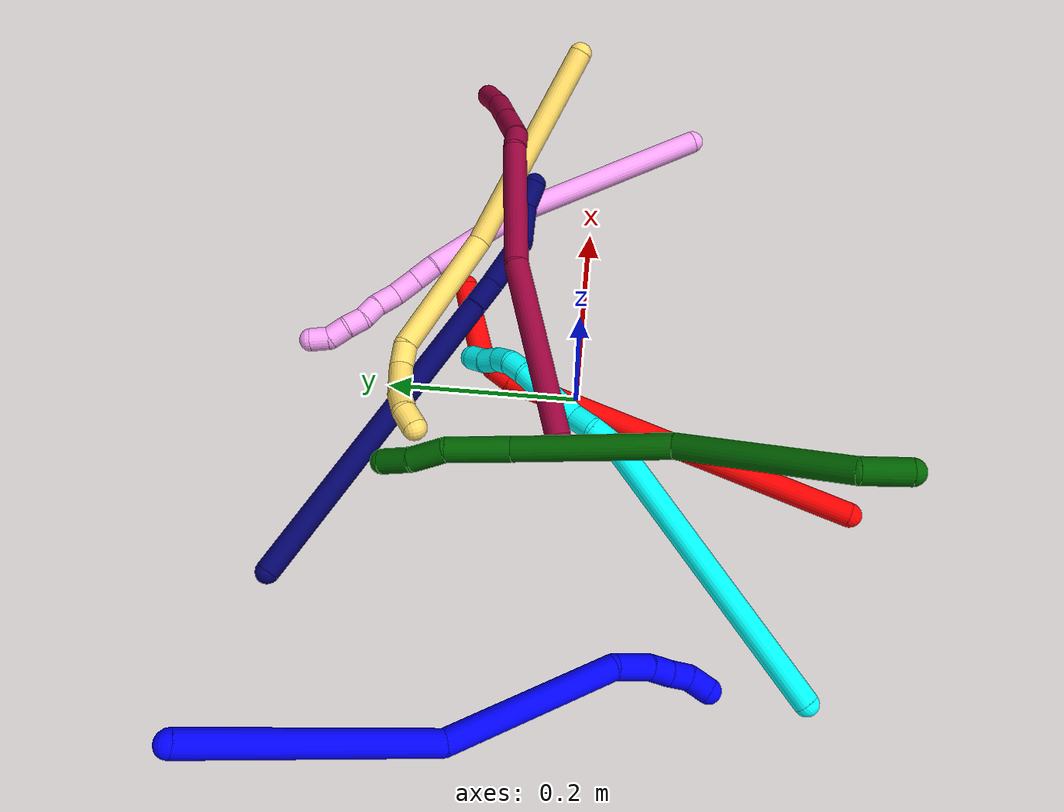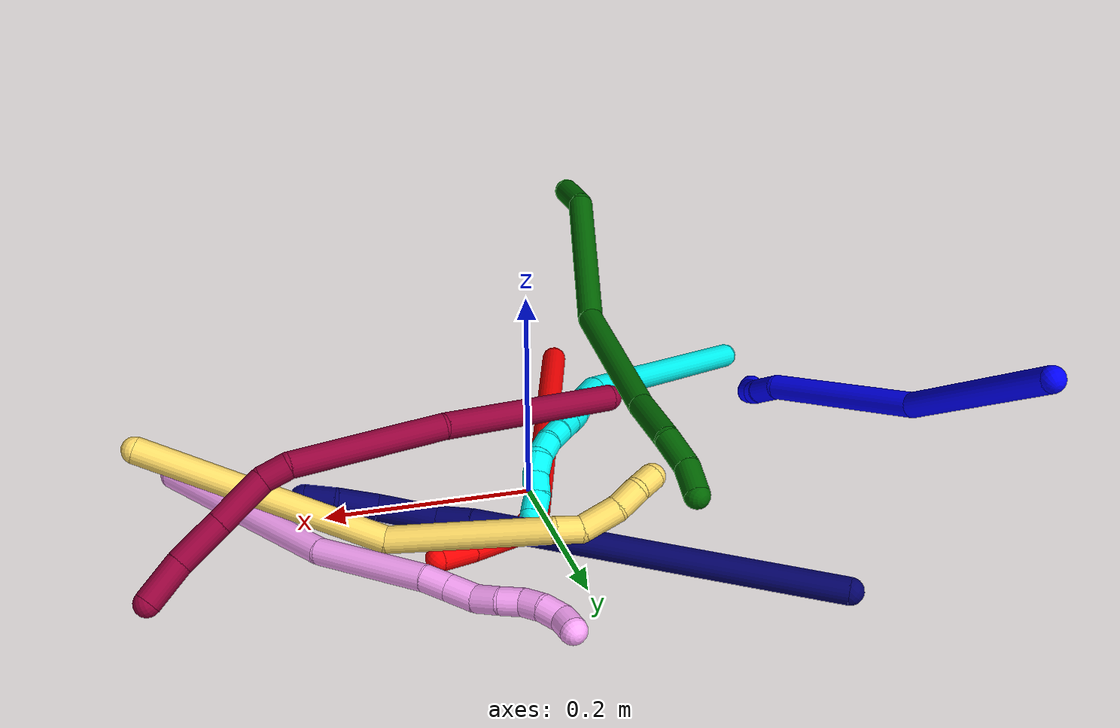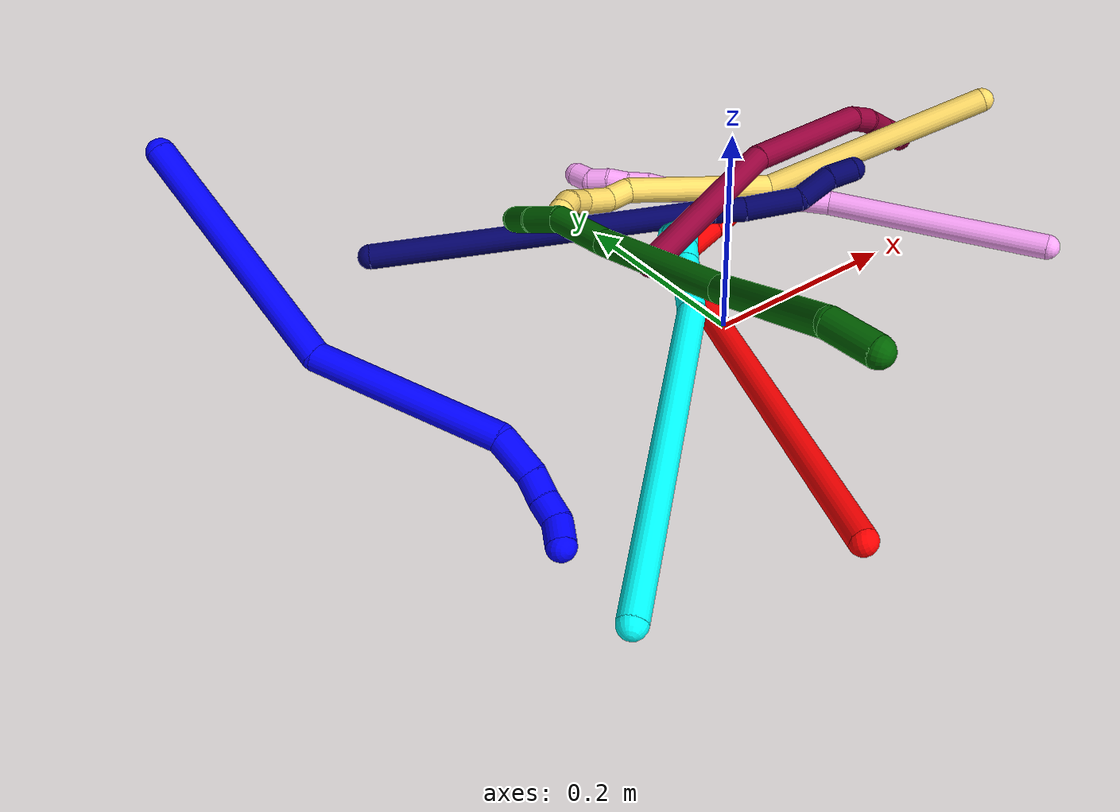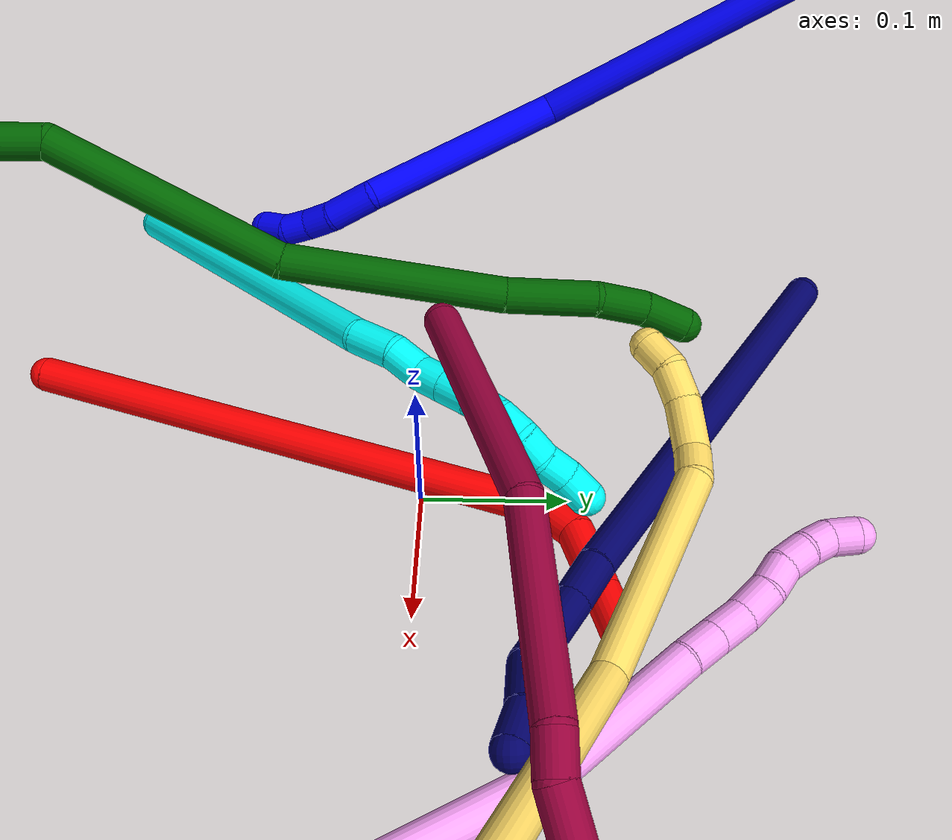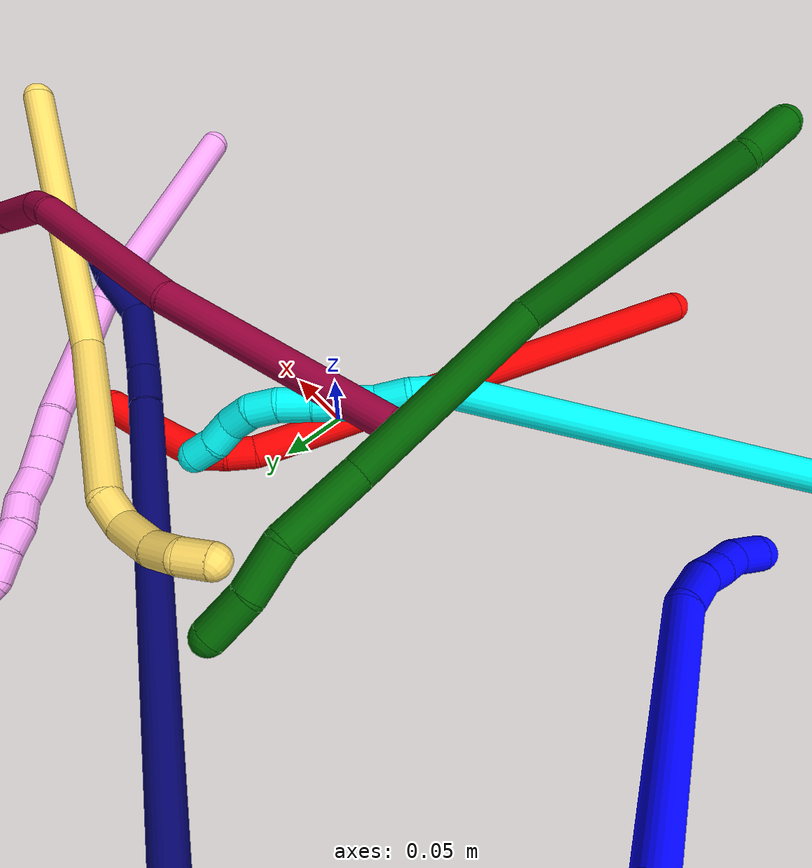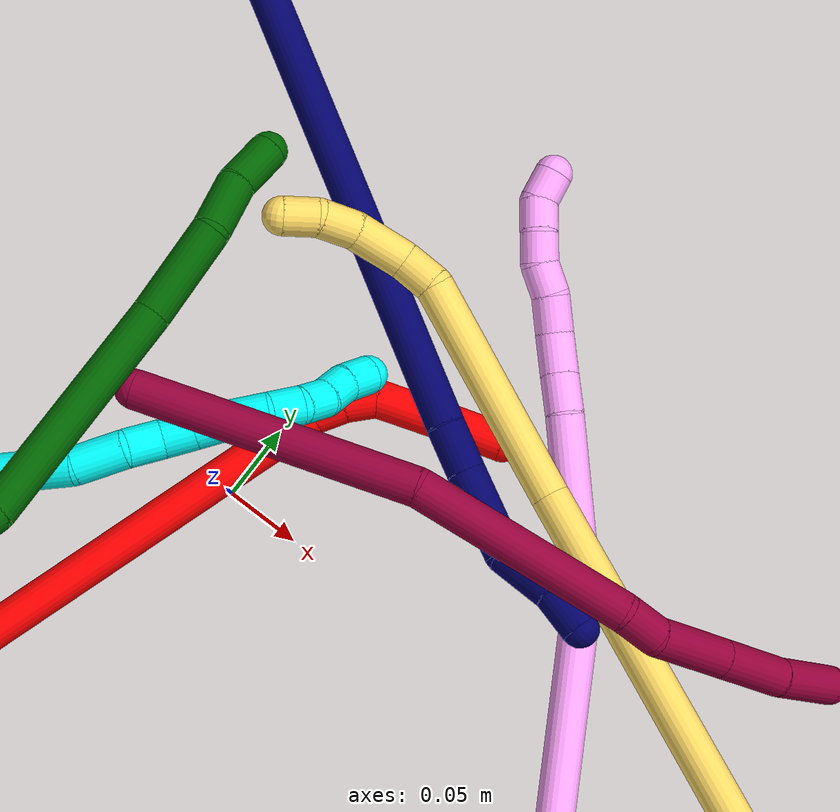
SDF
<sdf version="1.7">
 <world name="default">
  <plugin name="TubeGeneratorPlugin" filename="libtube_generator_plugin.so"/>
  <model name="photoneo_s_sensor">
   <static>1</static>
   <pose>0 0 2 1.57079 1.57079 3.14159</pose>
   <link name="link">
    <inertial><mass>0.1</mass></inertial>
    <sensor name="sensor" type="depth">
     <update_rate>30</update_rate>
     <camera>
      <horizontal_fov>1.22</horizontal_fov>
      <image><width>1920</width><height>1200</height><format>B8G8R8</format></image>
      <clip><near>0.1</near><far>4</far></clip>
      <depth_camera><output>points</output></depth_camera>
     </camera>
     <plugin name="camera_plugin" filename="libgazebo_ros_depth_camera.so">
      <baseline>0.2</baseline>
      <alwaysOn>1</alwaysOn>
      <updateRate>0.0</updateRate>
      <cameraName>camera_ir</cameraName>
      <imageTopicName>/camera/color/image_raw</imageTopicName>
      <cameraInfoTopicName>/camera/color/camera_info</cameraInfoTopicName>
      <depthImageTopicName>/camera/depth/image_raw</depthImageTopicName>
      <depthImageCameraInfoTopicName>/camera/depth/camera_info</depthImageCameraInfoTopicName>
      <pointCloudTopicName>/camera/depth/points</pointCloudTopicName>
      <frameName>fr_optical</frameName>
      <pointCloudCutoff>0.1</pointCloudCutoff>
      <pointCloudCutoffMax>2.0</pointCloudCutoffMax>
      <distortionK1>0</distortionK1>
      <distortionK2>0</distortionK2>
      <distortionK3>0</distortionK3>
      <distortionT1>0</distortionT1>
      <distortionT2>0</distortionT2>
      <CxPrime>0</CxPrime>
      <Cx>0</Cx>
      <Cy>0</Cy>
      <focalLength>0</focalLength>
      <hackBaseline>0</hackBaseline>
     </plugin>
    </sensor>
   </link>
  </model>
  <gravity>0 0 -9.8</gravity>
  <magnetic_field>6e-06 2.3e-05 -4.2e-05</magnetic_field>
  <atmosphere type="adiabatic"/>
  <physics name="default_physics" default="0" type="ode">
   <max_step_size>0.003</max_step_size>
   <real_time_factor>1</real_time_factor>
   <real_time_update_rate>1000</real_time_update_rate>
   <max_contacts>10000</max_contacts>
   <ode>
    <solver>
     <type>quick</type>
     <iters>100</iters>
     <sor>1.3</sor>
     <use_dynamic_moi_rescaling>0</use_dynamic_moi_rescaling>
    </solver>
    <constraints>
     <contact_max_correcting_vel>0</contact_max_correcting_vel>
     <contact_surface_layer>0.001</contact_surface_layer>
     <cfm>0</cfm>
     <erp>0.2</erp>
    </constraints>
   </ode>
  </physics>
  <scene><ambient>0.4 0.4 0.4 1</ambient><background>0.7 0.7 0.7 1</background><shadows>0</shadows></scene>
  <audio><device>default</device></audio>
  <spherical_coordinates>
   <surface_model>EARTH_WGS84</surface_model>
   <latitude_deg>0</latitude_deg>
   <longitude_deg>0</longitude_deg>
   <elevation>0</elevation>
   <heading_deg>0</heading_deg>
  </spherical_coordinates>
  <model name="bin">
   <static>1</static>
   <link name="bottom">
    <collision name="collision-bottom">
     <pose>0 0 -0.01 0 -0 0</pose>
     <geometry><box><size>0.8 0.6 0.02</size></box></geometry>
     <surface>
      <friction><ode><mu>100</mu><mu2>100</mu2></ode></friction>
      <contact><collide_bitmask>65535</collide_bitmask></contact>
     </surface>
    </collision>
   </link>
   <link name="west_wall">
    <collision name="collision-west_wall">
     <pose>-0.41 0 0.1 0 -0 0</pose>
     <geometry><box><size>0.02 0.6 0.2</size></box></geometry>
     <surface>
      <friction><ode><mu>100</mu><mu2>100</mu2></ode></friction>
      <contact><collide_bitmask>65535</collide_bitmask></contact>
     </surface>
    </collision>
   </link>
   <link name="east_wall">
    <collision name="collision-east_wall">
     <pose>0.41 0 0.1 0 -0 0</pose>
     <geometry><box><size>0.02 0.6 0.2</size></box></geometry>
     <surface>
      <friction><ode><mu>100</mu><mu2>100</mu2></ode></friction>
      <contact><collide_bitmask>65535</collide_bitmask></contact>
     </surface>
    </collision>
   </link>
   <link name="south_wall">
    <collision name="collision-south_wall">
     <pose>0 -0.31 0.1 0 -0 0</pose>
     <geometry><box><size>0.8 0.02 0.2</size></box></geometry>
     <surface>
      <friction><ode><mu>100</mu><mu2>100</mu2></ode></friction>
      <contact><collide_bitmask>65535</collide_bitmask></contact>
     </surface>
    </collision>
   </link>
   <link name="north_wall">
    <collision name="collision-north_wall">
     <pose>0 0.31 0.1 0 -0 0</pose>
     <geometry><box><size>0.8 0.02 0.2</size></box></geometry>
     <surface>
      <friction><ode><mu>100</mu><mu2>100</mu2></ode></friction>
      <contact><collide_bitmask>65535</collide_bitmask></contact>
     </surface>
    </collision>
   </link>
  </model>
  <model name="1">
   <static>0</static>
   <link name="1">
    <collision name="collision-cylinder-e_1_1_4">
     <pose>0.048468 -0.07131 -0.075218 2.38286 0.437412 1.01717</pose>
     <geometry><cylinder><radius>0.0125</radius><length>0.228841</length></cylinder></geometry>
     <surface>
      <friction><ode><mu>1.16</mu><mu2>1.16</mu2><slip1>0</slip1><slip2>0</slip2></ode></friction>
      <contact><ode><kp>1e+06</kp><kd>1</kd><max_vel>0</max_vel><min_depth>0.001</min_depth></ode></contact>
     </surface>
    </collision>
    <visual name="visual-cylinder-e_1_1_4">
     <pose>0.048468 -0.07131 -0.075218 2.38286 0.437412 1.01717</pose>
     <geometry><cylinder><radius>0.0125</radius><length>0.228841</length></cylinder></geometry>
     <material><ambient>0 0 1 1</ambient></material>
    </visual>
    <collision name="collision-cylinder-e_2_4_5">
     <pose>0.094325 -0.197481 -0.21391 2.42883 -0.031115 -0.083538</pose>
     <geometry><cylinder><radius>0.0125</radius><length>0.167875</length></cylinder></geometry>
     <surface>
      <friction><ode><mu>1.16</mu><mu2>1.16</mu2><slip1>0</slip1><slip2>0</slip2></ode></friction>
      <contact><ode><kp>1e+06</kp><kd>1</kd><max_vel>0</max_vel><min_depth>0.001</min_depth></ode></contact>
     </surface>
    </collision>
    <visual name="visual-cylinder-e_2_4_5">
     <pose>0.094325 -0.197481 -0.21391 2.42883 -0.031115 -0.083538</pose>
     <geometry><cylinder><radius>0.0125</radius><length>0.167875</length></cylinder></geometry>
     <material><ambient>0 0 1 1</ambient></material>
    </visual>
    <collision name="collision-cylinder-e_3_5_6">
     <pose>0.09937 -0.264411 -0.289961 2.3769 0.413858 0.962252</pose>
     <geometry><cylinder><radius>0.0125</radius><length>0.038077</length></cylinder></geometry>
     <surface>
      <friction><ode><mu>1.16</mu><mu2>1.16</mu2><slip1>0</slip1><slip2>0</slip2></ode></friction>
      <contact><ode><kp>1e+06</kp><kd>1</kd><max_vel>0</max_vel><min_depth>0.001</min_depth></ode></contact>
     </surface>
    </collision>
    <visual name="visual-cylinder-e_3_5_6">
     <pose>0.09937 -0.264411 -0.289961 2.3769 0.413858 0.962252</pose>
     <geometry><cylinder><radius>0.0125</radius><length>0.038077</length></cylinder></geometry>
     <material><ambient>0 0 1 1</ambient></material>
    </visual>
    <collision name="collision-cylinder-e_4_6_7">
     <pose>0.113656 -0.281678 -0.309768 2.5181 0.640002 1.59875</pose>
     <geometry><cylinder><radius>0.0125</radius><length>0.022202</length></cylinder></geometry>
     <surface>
      <friction><ode><mu>1.16</mu><mu2>1.16</mu2><slip1>0</slip1><slip2>0</slip2></ode></friction>
      <contact><ode><kp>1e+06</kp><kd>1</kd><max_vel>0</max_vel><min_depth>0.001</min_depth></ode></contact>
     </surface>
    </collision>
    <visual name="visual-cylinder-e_4_6_7">
     <pose>0.113656 -0.281678 -0.309768 2.5181 0.640002 1.59875</pose>
     <geometry><cylinder><radius>0.0125</radius><length>0.022202</length></cylinder></geometry>
     <material><ambient>0 0 1 1</ambient></material>
    </visual>
    <collision name="collision-cylinder-e_5_7_8">
     <pose>0.125444 -0.291468 -0.324789 2.60912 0.518392 1.54273</pose>
     <geometry><cylinder><radius>0.0125</radius><length>0.020824</length></cylinder></geometry>
     <surface>
      <friction><ode><mu>1.16</mu><mu2>1.16</mu2><slip1>0</slip1><slip2>0</slip2></ode></friction>
      <contact><ode><kp>1e+06</kp><kd>1</kd><max_vel>0</max_vel><min_depth>0.001</min_depth></ode></contact>
     </surface>
    </collision>
    <visual name="visual-cylinder-e_5_7_8">
     <pose>0.125444 -0.291468 -0.324789 2.60912 0.518392 1.54273</pose>
     <geometry><cylinder><radius>0.0125</radius><length>0.020824</length></cylinder></geometry>
     <material><ambient>0 0 1 1</ambient></material>
    </visual>
    <collision name="collision-cylinder-e_6_8_2">
     <pose>0.138305 -0.296747 -0.340531 3.05535 0.767705 2.92875</pose>
     <geometry><cylinder><radius>0.0125</radius><length>0.022182</length></cylinder></geometry>
     <surface>
      <friction><ode><mu>1.16</mu><mu2>1.16</mu2><slip1>0</slip1><slip2>0</slip2></ode></friction>
      <contact><ode><kp>1e+06</kp><kd>1</kd><max_vel>0</max_vel><min_depth>0.001</min_depth></ode></contact>
     </surface>
    </collision>
    <visual name="visual-cylinder-e_6_8_2">
     <pose>0.138305 -0.296747 -0.340531 3.05535 0.767705 2.92875</pose>
     <geometry><cylinder><radius>0.0125</radius><length>0.022182</length></cylinder></geometry>
     <material><ambient>0 0 1 1</ambient></material>
    </visual>
    <collision name="collision-sphere-2">
     <pose>0.146008 -0.297434 -0.348481 0 -0 0</pose>
     <geometry><sphere><radius>0.0125</radius></sphere></geometry>
     <surface>
      <friction><ode><mu>1.16</mu><mu2>1.16</mu2><slip1>0</slip1><slip2>0</slip2></ode></friction>
      <contact><ode><kp>1e+06</kp><kd>1</kd><max_vel>0</max_vel><min_depth>0.001</min_depth></ode></contact>
     </surface>
    </collision>
    <visual name="visual-sphere-2">
     <pose>0.146008 -0.297434 -0.348481 0 -0 0</pose>
     <geometry><sphere><radius>0.0125</radius></sphere></geometry>
     <material><ambient>0 0 1 1</ambient></material>
    </visual>
    <collision name="collision-sphere-4">
     <pose>0.096936 -0.142619 -0.150437 0 -0 0</pose>
     <geometry><sphere><radius>0.0125</radius></sphere></geometry>
     <surface>
      <friction><ode><mu>1.16</mu><mu2>1.16</mu2><slip1>0</slip1><slip2>0</slip2></ode></friction>
      <contact><ode><kp>1e+06</kp><kd>1</kd><max_vel>0</max_vel><min_depth>0.001</min_depth></ode></contact>
     </surface>
    </collision>
    <visual name="visual-sphere-4">
     <pose>0.096936 -0.142619 -0.150437 0 -0 0</pose>
     <geometry><sphere><radius>0.0125</radius></sphere></geometry>
     <material><ambient>0 0 1 1</ambient></material>
    </visual>
    <collision name="collision-sphere-1">
     <geometry><sphere><radius>0.0125</radius></sphere></geometry>
     <surface>
      <friction><ode><mu>1.16</mu><mu2>1.16</mu2><slip1>0</slip1><slip2>0</slip2></ode></friction>
      <contact><ode><kp>1e+06</kp><kd>1</kd><max_vel>0</max_vel><min_depth>0.001</min_depth></ode></contact>
     </surface>
    </collision>
    <visual name="visual-sphere-1">
     <geometry><sphere><radius>0.0125</radius></sphere></geometry>
     <material><ambient>0 0 1 1</ambient></material>
    </visual>
    <collision name="collision-sphere-8">
     <pose>0.130603 -0.29606 -0.33258 0 -0 0</pose>
     <geometry><sphere><radius>0.0125</radius></sphere></geometry>
     <surface>
      <friction><ode><mu>1.16</mu><mu2>1.16</mu2><slip1>0</slip1><slip2>0</slip2></ode></friction>
      <contact><ode><kp>1e+06</kp><kd>1</kd><max_vel>0</max_vel><min_depth>0.001</min_depth></ode></contact>
     </surface>
    </collision>
    <visual name="visual-sphere-8">
     <pose>0.130603 -0.29606 -0.33258 0 -0 0</pose>
     <geometry><sphere><radius>0.0125</radius></sphere></geometry>
     <material><ambient>0 0 1 1</ambient></material>
    </visual>
    <collision name="collision-sphere-5">
     <pose>0.091714 -0.252343 -0.277383 0 -0 0</pose>
     <geometry><sphere><radius>0.0125</radius></sphere></geometry>
     <surface>
      <friction><ode><mu>1.16</mu><mu2>1.16</mu2><slip1>0</slip1><slip2>0</slip2></ode></friction>
      <contact><ode><kp>1e+06</kp><kd>1</kd><max_vel>0</max_vel><min_depth>0.001</min_depth></ode></contact>
     </surface>
    </collision>
    <visual name="visual-sphere-5">
     <pose>0.091714 -0.252343 -0.277383 0 -0 0</pose>
     <geometry><sphere><radius>0.0125</radius></sphere></geometry>
     <material><ambient>0 0 1 1</ambient></material>
    </visual>
    <collision name="collision-sphere-6">
     <pose>0.107026 -0.27648 -0.30254 0 -0 0</pose>
     <geometry><sphere><radius>0.0125</radius></sphere></geometry>
     <surface>
      <friction><ode><mu>1.16</mu><mu2>1.16</mu2><slip1>0</slip1><slip2>0</slip2></ode></friction>
      <contact><ode><kp>1e+06</kp><kd>1</kd><max_vel>0</max_vel><min_depth>0.001</min_depth></ode></contact>
     </surface>
    </collision>
    <visual name="visual-sphere-6">
     <pose>0.107026 -0.27648 -0.30254 0 -0 0</pose>
     <geometry><sphere><radius>0.0125</radius></sphere></geometry>
     <material><ambient>0 0 1 1</ambient></material>
    </visual>
    <collision name="collision-sphere-7">
     <pose>0.120285 -0.286877 -0.316997 0 -0 0</pose>
     <geometry><sphere><radius>0.0125</radius></sphere></geometry>
     <surface>
      <friction><ode><mu>1.16</mu><mu2>1.16</mu2><slip1>0</slip1><slip2>0</slip2></ode></friction>
      <contact><ode><kp>1e+06</kp><kd>1</kd><max_vel>0</max_vel><min_depth>0.001</min_depth></ode></contact>
     </surface>
    </collision>
    <visual name="visual-sphere-7">
     <pose>0.120285 -0.286877 -0.316997 0 -0 0</pose>
     <geometry><sphere><radius>0.0125</radius></sphere></geometry>
     <material><ambient>0 0 1 1</ambient></material>
    </visual>
    <inertial>
     <pose>0.077827 -0.156889 -0.170717 0 -0 0</pose>
     <mass>0.5</mass>
     <inertia>
      <ixx>0.001643</ixx>
      <ixy>0</ixy>
      <ixz>0</ixz>
      <iyy>0.000293</iyy>
      <iyz>0</iyz>
      <izz>0.000448</izz>
     </inertia>
    </inertial>
   </link>
   <pose>-0.387751 0.288505 0.190858 2.02529 0.636379 -2.80656</pose>
  </model>
  <model name="2">
   <static>0</static>
   <link name="2">
    <collision name="collision-cylinder-e_1_1_4">
     <pose>0.112734 0.11297 -0.096123 -2.27579 0.649885 -1.25981</pose>
     <geometry><cylinder><radius>0.0125</radius><length>0.372617</length></cylinder></geometry>
     <surface>
      <friction><ode><mu>1.16</mu><mu2>1.16</mu2><slip1>0</slip1><slip2>0</slip2></ode></friction>
      <contact><ode><kp>1e+06</kp><kd>1</kd><max_vel>0</max_vel><min_depth>0.001</min_depth></ode></contact>
     </surface>
    </collision>
    <visual name="visual-cylinder-e_1_1_4">
     <pose>0.112734 0.11297 -0.096123 -2.27579 0.649885 -1.25981</pose>
     <geometry><cylinder><radius>0.0125</radius><length>0.372617</length></cylinder></geometry>
     <material><ambient>1 0 0 1</ambient></material>
    </visual>
    <collision name="collision-cylinder-e_2_4_5">
     <pose>0.233114 0.23275 -0.195257 -1.98722 0.798583 -1.14995</pose>
     <geometry><cylinder><radius>0.0125</radius><length>0.021344</length></cylinder></geometry>
     <surface>
      <friction><ode><mu>1.16</mu><mu2>1.16</mu2><slip1>0</slip1><slip2>0</slip2></ode></friction>
      <contact><ode><kp>1e+06</kp><kd>1</kd><max_vel>0</max_vel><min_depth>0.001</min_depth></ode></contact>
     </surface>
    </collision>
    <visual name="visual-cylinder-e_2_4_5">
     <pose>0.233114 0.23275 -0.195257 -1.98722 0.798583 -1.14995</pose>
     <geometry><cylinder><radius>0.0125</radius><length>0.021344</length></cylinder></geometry>
     <material><ambient>1 0 0 1</ambient></material>
    </visual>
    <collision name="collision-cylinder-e_3_5_6">
     <pose>0.249612 0.245153 -0.199879 -1.85112 0.989175 -1.24339</pose>
     <geometry><cylinder><radius>0.0125</radius><length>0.02119</length></cylinder></geometry>
     <surface>
      <friction><ode><mu>1.16</mu><mu2>1.16</mu2><slip1>0</slip1><slip2>0</slip2></ode></friction>
      <contact><ode><kp>1e+06</kp><kd>1</kd><max_vel>0</max_vel><min_depth>0.001</min_depth></ode></contact>
     </surface>
    </collision>
    <visual name="visual-cylinder-e_3_5_6">
     <pose>0.249612 0.245153 -0.199879 -1.85112 0.989175 -1.24339</pose>
     <geometry><cylinder><radius>0.0125</radius><length>0.02119</length></cylinder></geometry>
     <material><ambient>1 0 0 1</ambient></material>
    </visual>
    <collision name="collision-cylinder-e_4_6_7">
     <pose>0.282175 0.257811 -0.19513 -0.837826 1.18953 -0.585145</pose>
     <geometry><cylinder><radius>0.0125</radius><length>0.05109</length></cylinder></geometry>
     <surface>
      <friction><ode><mu>1.16</mu><mu2>1.16</mu2><slip1>0</slip1><slip2>0</slip2></ode></friction>
      <contact><ode><kp>1e+06</kp><kd>1</kd><max_vel>0</max_vel><min_depth>0.001</min_depth></ode></contact>
     </surface>
    </collision>
    <visual name="visual-cylinder-e_4_6_7">
     <pose>0.282175 0.257811 -0.19513 -0.837826 1.18953 -0.585145</pose>
     <geometry><cylinder><radius>0.0125</radius><length>0.05109</length></cylinder></geometry>
     <material><ambient>1 0 0 1</ambient></material>
    </visual>
    <collision name="collision-cylinder-e_5_7_2">
     <pose>0.321139 0.270077 -0.18375 -0.803155 1.1282 -0.524943</pose>
     <geometry><cylinder><radius>0.0125</radius><length>0.033759</length></cylinder></geometry>
     <surface>
      <friction><ode><mu>1.16</mu><mu2>1.16</mu2><slip1>0</slip1><slip2>0</slip2></ode></friction>
      <contact><ode><kp>1e+06</kp><kd>1</kd><max_vel>0</max_vel><min_depth>0.001</min_depth></ode></contact>
     </surface>
    </collision>
    <visual name="visual-cylinder-e_5_7_2">
     <pose>0.321139 0.270077 -0.18375 -0.803155 1.1282 -0.524943</pose>
     <geometry><cylinder><radius>0.0125</radius><length>0.033759</length></cylinder></geometry>
     <material><ambient>1 0 0 1</ambient></material>
    </visual>
    <collision name="collision-sphere-2">
     <pose>0.336392 0.275278 -0.17873 0 -0 0</pose>
     <geometry><sphere><radius>0.0125</radius></sphere></geometry>
     <surface>
      <friction><ode><mu>1.16</mu><mu2>1.16</mu2><slip1>0</slip1><slip2>0</slip2></ode></friction>
      <contact><ode><kp>1e+06</kp><kd>1</kd><max_vel>0</max_vel><min_depth>0.001</min_depth></ode></contact>
     </surface>
    </collision>
    <visual name="visual-sphere-2">
     <pose>0.336392 0.275278 -0.17873 0 -0 0</pose>
     <geometry><sphere><radius>0.0125</radius></sphere></geometry>
     <material><ambient>1 0 0 1</ambient></material>
    </visual>
    <collision name="collision-sphere-7">
     <pose>0.305886 0.264875 -0.188771 0 -0 0</pose>
     <geometry><sphere><radius>0.0125</radius></sphere></geometry>
     <surface>
      <friction><ode><mu>1.16</mu><mu2>1.16</mu2><slip1>0</slip1><slip2>0</slip2></ode></friction>
      <contact><ode><kp>1e+06</kp><kd>1</kd><max_vel>0</max_vel><min_depth>0.001</min_depth></ode></contact>
     </surface>
    </collision>
    <visual name="visual-sphere-7">
     <pose>0.305886 0.264875 -0.188771 0 -0 0</pose>
     <geometry><sphere><radius>0.0125</radius></sphere></geometry>
     <material><ambient>1 0 0 1</ambient></material>
    </visual>
    <collision name="collision-sphere-6">
     <pose>0.258465 0.250747 -0.20149 0 -0 0</pose>
     <geometry><sphere><radius>0.0125</radius></sphere></geometry>
     <surface>
      <friction><ode><mu>1.16</mu><mu2>1.16</mu2><slip1>0</slip1><slip2>0</slip2></ode></friction>
      <contact><ode><kp>1e+06</kp><kd>1</kd><max_vel>0</max_vel><min_depth>0.001</min_depth></ode></contact>
     </surface>
    </collision>
    <visual name="visual-sphere-6">
     <pose>0.258465 0.250747 -0.20149 0 -0 0</pose>
     <geometry><sphere><radius>0.0125</radius></sphere></geometry>
     <material><ambient>1 0 0 1</ambient></material>
    </visual>
    <collision name="collision-sphere-5">
     <pose>0.240759 0.23956 -0.198269 0 -0 0</pose>
     <geometry><sphere><radius>0.0125</radius></sphere></geometry>
     <surface>
      <friction><ode><mu>1.16</mu><mu2>1.16</mu2><slip1>0</slip1><slip2>0</slip2></ode></friction>
      <contact><ode><kp>1e+06</kp><kd>1</kd><max_vel>0</max_vel><min_depth>0.001</min_depth></ode></contact>
     </surface>
    </collision>
    <visual name="visual-sphere-5">
     <pose>0.240759 0.23956 -0.198269 0 -0 0</pose>
     <geometry><sphere><radius>0.0125</radius></sphere></geometry>
     <material><ambient>1 0 0 1</ambient></material>
    </visual>
    <collision name="collision-sphere-1">
     <geometry><sphere><radius>0.0125</radius></sphere></geometry>
     <surface>
      <friction><ode><mu>1.16</mu><mu2>1.16</mu2><slip1>0</slip1><slip2>0</slip2></ode></friction>
      <contact><ode><kp>1e+06</kp><kd>1</kd><max_vel>0</max_vel><min_depth>0.001</min_depth></ode></contact>
     </surface>
    </collision>
    <visual name="visual-sphere-1">
     <geometry><sphere><radius>0.0125</radius></sphere></geometry>
     <material><ambient>1 0 0 1</ambient></material>
    </visual>
    <collision name="collision-sphere-4">
     <pose>0.225469 0.22594 -0.192245 0 -0 0</pose>
     <geometry><sphere><radius>0.0125</radius></sphere></geometry>
     <surface>
      <friction><ode><mu>1.16</mu><mu2>1.16</mu2><slip1>0</slip1><slip2>0</slip2></ode></friction>
      <contact><ode><kp>1e+06</kp><kd>1</kd><max_vel>0</max_vel><min_depth>0.001</min_depth></ode></contact>
     </surface>
    </collision>
    <visual name="visual-sphere-4">
     <pose>0.225469 0.22594 -0.192245 0 -0 0</pose>
     <geometry><sphere><radius>0.0125</radius></sphere></geometry>
     <material><ambient>1 0 0 1</ambient></material>
    </visual>
    <inertial>
     <pose>0.155059 0.149093 -0.120785 0 -0 0</pose>
     <mass>0.5</mass>
     <inertia>
      <ixx>-0.002198</ixx>
      <ixy>0</ixy>
      <ixz>0</ixz>
      <iyy>-0.002204</iyy>
      <iyz>0</iyz>
      <izz>-0.00528</izz>
     </inertia>
    </inertial>
   </link>
   <pose>-0.105724 -0.282626 0.012535 1.03086 0.402924 0.39604</pose>
  </model>
  <model name="3">
   <static>0</static>
   <link name="3">
    <collision name="collision-cylinder-e_1_1_4">
     <pose>-0.005827 -0.00252 -0.147366 3.1245 -0.039512 -2.32493</pose>
     <geometry><cylinder><radius>0.0125</radius><length>0.295006</length></cylinder></geometry>
     <surface>
      <friction><ode><mu>1.16</mu><mu2>1.16</mu2><slip1>0</slip1><slip2>0</slip2></ode></friction>
      <contact><ode><kp>1e+06</kp><kd>1</kd><max_vel>0</max_vel><min_depth>0.001</min_depth></ode></contact>
     </surface>
    </collision>
    <visual name="visual-cylinder-e_1_1_4">
     <pose>-0.005827 -0.00252 -0.147366 3.1245 -0.039512 -2.32493</pose>
     <geometry><cylinder><radius>0.0125</radius><length>0.295006</length></cylinder></geometry>
     <material><ambient>0.003922 1 0.996078 1</ambient></material>
    </visual>
    <collision name="collision-cylinder-e_2_4_5">
     <pose>-0.007733 -0.005914 -0.310578 3.08644 0.242151 2.69575</pose>
     <geometry><cylinder><radius>0.0125</radius><length>0.032694</length></cylinder></geometry>
     <surface>
      <friction><ode><mu>1.16</mu><mu2>1.16</mu2><slip1>0</slip1><slip2>0</slip2></ode></friction>
      <contact><ode><kp>1e+06</kp><kd>1</kd><max_vel>0</max_vel><min_depth>0.001</min_depth></ode></contact>
     </surface>
    </collision>
    <visual name="visual-cylinder-e_2_4_5">
     <pose>-0.007733 -0.005914 -0.310578 3.08644 0.242151 2.69575</pose>
     <geometry><cylinder><radius>0.0125</radius><length>0.032694</length></cylinder></geometry>
     <material><ambient>0.003922 1 0.996078 1</ambient></material>
    </visual>
    <collision name="collision-cylinder-e_3_5_6">
     <pose>0.001224 -0.004181 -0.336895 -2.89754 0.436748 -2.13187</pose>
     <geometry><cylinder><radius>0.0125</radius><length>0.023818</length></cylinder></geometry>
     <surface>
      <friction><ode><mu>1.16</mu><mu2>1.16</mu2><slip1>0</slip1><slip2>0</slip2></ode></friction>
      <contact><ode><kp>1e+06</kp><kd>1</kd><max_vel>0</max_vel><min_depth>0.001</min_depth></ode></contact>
     </surface>
    </collision>
    <visual name="visual-cylinder-e_3_5_6">
     <pose>0.001224 -0.004181 -0.336895 -2.89754 0.436748 -2.13187</pose>
     <geometry><cylinder><radius>0.0125</radius><length>0.023818</length></cylinder></geometry>
     <material><ambient>0.003922 1 0.996078 1</ambient></material>
    </visual>
    <collision name="collision-cylinder-e_4_6_7">
     <pose>0.008571 -0.001593 -0.357797 3.13978 0.217905 3.12497</pose>
     <geometry><cylinder><radius>0.0125</radius><length>0.021366</length></cylinder></geometry>
     <surface>
      <friction><ode><mu>1.16</mu><mu2>1.16</mu2><slip1>0</slip1><slip2>0</slip2></ode></friction>
      <contact><ode><kp>1e+06</kp><kd>1</kd><max_vel>0</max_vel><min_depth>0.001</min_depth></ode></contact>
     </surface>
    </collision>
    <visual name="visual-cylinder-e_4_6_7">
     <pose>0.008571 -0.001593 -0.357797 3.13978 0.217905 3.12497</pose>
     <geometry><cylinder><radius>0.0125</radius><length>0.021366</length></cylinder></geometry>
     <material><ambient>0.003922 1 0.996078 1</ambient></material>
    </visual>
    <collision name="collision-cylinder-e_5_7_8">
     <pose>0.013365 -0.001758 -0.379652 3.1288 0.214151 3.02276</pose>
     <geometry><cylinder><radius>0.0125</radius><length>0.023385</length></cylinder></geometry>
     <surface>
      <friction><ode><mu>1.16</mu><mu2>1.16</mu2><slip1>0</slip1><slip2>0</slip2></ode></friction>
      <contact><ode><kp>1e+06</kp><kd>1</kd><max_vel>0</max_vel><min_depth>0.001</min_depth></ode></contact>
     </surface>
    </collision>
    <visual name="visual-cylinder-e_5_7_8">
     <pose>0.013365 -0.001758 -0.379652 3.1288 0.214151 3.02276</pose>
     <geometry><cylinder><radius>0.0125</radius><length>0.023385</length></cylinder></geometry>
     <material><ambient>0.003922 1 0.996078 1</ambient></material>
    </visual>
    <collision name="collision-cylinder-e_6_8_9">
     <pose>0.018372 -0.000761 -0.402277 -3.03991 0.220363 -2.27936</pose>
     <geometry><cylinder><radius>0.0125</radius><length>0.023076</length></cylinder></geometry>
     <surface>
      <friction><ode><mu>1.16</mu><mu2>1.16</mu2><slip1>0</slip1><slip2>0</slip2></ode></friction>
      <contact><ode><kp>1e+06</kp><kd>1</kd><max_vel>0</max_vel><min_depth>0.001</min_depth></ode></contact>
     </surface>
    </collision>
    <visual name="visual-cylinder-e_6_8_9">
     <pose>0.018372 -0.000761 -0.402277 -3.03991 0.220363 -2.27936</pose>
     <geometry><cylinder><radius>0.0125</radius><length>0.023076</length></cylinder></geometry>
     <material><ambient>0.003922 1 0.996078 1</ambient></material>
    </visual>
    <collision name="collision-cylinder-e_7_9_10">
     <pose>0.025058 0.003279 -0.422403 -2.8277 0.417658 -1.85878</pose>
     <geometry><cylinder><radius>0.0125</radius><length>0.020531</length></cylinder></geometry>
     <surface>
      <friction><ode><mu>1.16</mu><mu2>1.16</mu2><slip1>0</slip1><slip2>0</slip2></ode></friction>
      <contact><ode><kp>1e+06</kp><kd>1</kd><max_vel>0</max_vel><min_depth>0.001</min_depth></ode></contact>
     </surface>
    </collision>
    <visual name="visual-cylinder-e_7_9_10">
     <pose>0.025058 0.003279 -0.422403 -2.8277 0.417658 -1.85878</pose>
     <geometry><cylinder><radius>0.0125</radius><length>0.020531</length></cylinder></geometry>
     <material><ambient>0.003922 1 0.996078 1</ambient></material>
    </visual>
    <collision name="collision-cylinder-e_8_10_11">
     <pose>0.035792 0.010656 -0.437461 -2.51075 0.713107 -1.70271</pose>
     <geometry><cylinder><radius>0.0125</radius><length>0.020085</length></cylinder></geometry>
     <surface>
      <friction><ode><mu>1.16</mu><mu2>1.16</mu2><slip1>0</slip1><slip2>0</slip2></ode></friction>
      <contact><ode><kp>1e+06</kp><kd>1</kd><max_vel>0</max_vel><min_depth>0.001</min_depth></ode></contact>
     </surface>
    </collision>
    <visual name="visual-cylinder-e_8_10_11">
     <pose>0.035792 0.010656 -0.437461 -2.51075 0.713107 -1.70271</pose>
     <geometry><cylinder><radius>0.0125</radius><length>0.020085</length></cylinder></geometry>
     <material><ambient>0.003922 1 0.996078 1</ambient></material>
    </visual>
    <collision name="collision-cylinder-e_9_11_12">
     <pose>0.050691 0.017739 -0.448487 -2.65263 0.983787 -2.27012</pose>
     <geometry><cylinder><radius>0.0125</radius><length>0.020009</length></cylinder></geometry>
     <surface>
      <friction><ode><mu>1.16</mu><mu2>1.16</mu2><slip1>0</slip1><slip2>0</slip2></ode></friction>
      <contact><ode><kp>1e+06</kp><kd>1</kd><max_vel>0</max_vel><min_depth>0.001</min_depth></ode></contact>
     </surface>
    </collision>
    <visual name="visual-cylinder-e_9_11_12">
     <pose>0.050691 0.017739 -0.448487 -2.65263 0.983787 -2.27012</pose>
     <geometry><cylinder><radius>0.0125</radius><length>0.020009</length></cylinder></geometry>
     <material><ambient>0.003922 1 0.996078 1</ambient></material>
    </visual>
    <collision name="collision-cylinder-e_10_12_2">
     <pose>0.065573 0.024146 -0.459929 -2.6155 0.713093 -1.88961</pose>
     <geometry><cylinder><radius>0.0125</radius><length>0.02003</length></cylinder></geometry>
     <surface>
      <friction><ode><mu>1.16</mu><mu2>1.16</mu2><slip1>0</slip1><slip2>0</slip2></ode></friction>
      <contact><ode><kp>1e+06</kp><kd>1</kd><max_vel>0</max_vel><min_depth>0.001</min_depth></ode></contact>
     </surface>
    </collision>
    <visual name="visual-cylinder-e_10_12_2">
     <pose>0.065573 0.024146 -0.459929 -2.6155 0.713093 -1.88961</pose>
     <geometry><cylinder><radius>0.0125</radius><length>0.02003</length></cylinder></geometry>
     <material><ambient>0.003922 1 0.996078 1</ambient></material>
    </visual>
    <collision name="collision-sphere-2">
     <pose>0.072124 0.027949 -0.46648 0 -0 0</pose>
     <geometry><sphere><radius>0.0125</radius></sphere></geometry>
     <surface>
      <friction><ode><mu>1.16</mu><mu2>1.16</mu2><slip1>0</slip1><slip2>0</slip2></ode></friction>
      <contact><ode><kp>1e+06</kp><kd>1</kd><max_vel>0</max_vel><min_depth>0.001</min_depth></ode></contact>
     </surface>
    </collision>
    <visual name="visual-sphere-2">
     <pose>0.072124 0.027949 -0.46648 0 -0 0</pose>
     <geometry><sphere><radius>0.0125</radius></sphere></geometry>
     <material><ambient>0.003922 1 0.996078 1</ambient></material>
    </visual>
    <collision name="collision-sphere-12">
     <pose>0.059021 0.020342 -0.453379 0 -0 0</pose>
     <geometry><sphere><radius>0.0125</radius></sphere></geometry>
     <surface>
      <friction><ode><mu>1.16</mu><mu2>1.16</mu2><slip1>0</slip1><slip2>0</slip2></ode></friction>
      <contact><ode><kp>1e+06</kp><kd>1</kd><max_vel>0</max_vel><min_depth>0.001</min_depth></ode></contact>
     </surface>
    </collision>
    <visual name="visual-sphere-12">
     <pose>0.059021 0.020342 -0.453379 0 -0 0</pose>
     <geometry><sphere><radius>0.0125</radius></sphere></geometry>
     <material><ambient>0.003922 1 0.996078 1</ambient></material>
    </visual>
    <collision name="collision-sphere-11">
     <pose>0.042361 0.015136 -0.443595 0 -0 0</pose>
     <geometry><sphere><radius>0.0125</radius></sphere></geometry>
     <surface>
      <friction><ode><mu>1.16</mu><mu2>1.16</mu2><slip1>0</slip1><slip2>0</slip2></ode></friction>
      <contact><ode><kp>1e+06</kp><kd>1</kd><max_vel>0</max_vel><min_depth>0.001</min_depth></ode></contact>
     </surface>
    </collision>
    <visual name="visual-sphere-11">
     <pose>0.042361 0.015136 -0.443595 0 -0 0</pose>
     <geometry><sphere><radius>0.0125</radius></sphere></geometry>
     <material><ambient>0.003922 1 0.996078 1</ambient></material>
    </visual>
    <collision name="collision-sphere-10">
     <pose>0.029222 0.006176 -0.431327 0 -0 0</pose>
     <geometry><sphere><radius>0.0125</radius></sphere></geometry>
     <surface>
      <friction><ode><mu>1.16</mu><mu2>1.16</mu2><slip1>0</slip1><slip2>0</slip2></ode></friction>
      <contact><ode><kp>1e+06</kp><kd>1</kd><max_vel>0</max_vel><min_depth>0.001</min_depth></ode></contact>
     </surface>
    </collision>
    <visual name="visual-sphere-10">
     <pose>0.029222 0.006176 -0.431327 0 -0 0</pose>
     <geometry><sphere><radius>0.0125</radius></sphere></geometry>
     <material><ambient>0.003922 1 0.996078 1</ambient></material>
    </visual>
    <collision name="collision-sphere-9">
     <pose>0.020894 0.000382 -0.413478 0 -0 0</pose>
     <geometry><sphere><radius>0.0125</radius></sphere></geometry>
     <surface>
      <friction><ode><mu>1.16</mu><mu2>1.16</mu2><slip1>0</slip1><slip2>0</slip2></ode></friction>
      <contact><ode><kp>1e+06</kp><kd>1</kd><max_vel>0</max_vel><min_depth>0.001</min_depth></ode></contact>
     </surface>
    </collision>
    <visual name="visual-sphere-9">
     <pose>0.020894 0.000382 -0.413478 0 -0 0</pose>
     <geometry><sphere><radius>0.0125</radius></sphere></geometry>
     <material><ambient>0.003922 1 0.996078 1</ambient></material>
    </visual>
    <collision name="collision-sphere-4">
     <pose>-0.011653 -0.005039 -0.294733 0 -0 0</pose>
     <geometry><sphere><radius>0.0125</radius></sphere></geometry>
     <surface>
      <friction><ode><mu>1.16</mu><mu2>1.16</mu2><slip1>0</slip1><slip2>0</slip2></ode></friction>
      <contact><ode><kp>1e+06</kp><kd>1</kd><max_vel>0</max_vel><min_depth>0.001</min_depth></ode></contact>
     </surface>
    </collision>
    <visual name="visual-sphere-4">
     <pose>-0.011653 -0.005039 -0.294733 0 -0 0</pose>
     <geometry><sphere><radius>0.0125</radius></sphere></geometry>
     <material><ambient>0.003922 1 0.996078 1</ambient></material>
    </visual>
    <collision name="collision-sphere-1">
     <geometry><sphere><radius>0.0125</radius></sphere></geometry>
     <surface>
      <friction><ode><mu>1.16</mu><mu2>1.16</mu2><slip1>0</slip1><slip2>0</slip2></ode></friction>
      <contact><ode><kp>1e+06</kp><kd>1</kd><max_vel>0</max_vel><min_depth>0.001</min_depth></ode></contact>
     </surface>
    </collision>
    <visual name="visual-sphere-1">
     <geometry><sphere><radius>0.0125</radius></sphere></geometry>
     <material><ambient>0.003922 1 0.996078 1</ambient></material>
    </visual>
    <collision name="collision-sphere-8">
     <pose>0.01585 -0.001904 -0.391077 0 -0 0</pose>
     <geometry><sphere><radius>0.0125</radius></sphere></geometry>
     <surface>
      <friction><ode><mu>1.16</mu><mu2>1.16</mu2><slip1>0</slip1><slip2>0</slip2></ode></friction>
      <contact><ode><kp>1e+06</kp><kd>1</kd><max_vel>0</max_vel><min_depth>0.001</min_depth></ode></contact>
     </surface>
    </collision>
    <visual name="visual-sphere-8">
     <pose>0.01585 -0.001904 -0.391077 0 -0 0</pose>
     <geometry><sphere><radius>0.0125</radius></sphere></geometry>
     <material><ambient>0.003922 1 0.996078 1</ambient></material>
    </visual>
    <collision name="collision-sphere-5">
     <pose>-0.003814 -0.006789 -0.326424 0 -0 0</pose>
     <geometry><sphere><radius>0.0125</radius></sphere></geometry>
     <surface>
      <friction><ode><mu>1.16</mu><mu2>1.16</mu2><slip1>0</slip1><slip2>0</slip2></ode></friction>
      <contact><ode><kp>1e+06</kp><kd>1</kd><max_vel>0</max_vel><min_depth>0.001</min_depth></ode></contact>
     </surface>
    </collision>
    <visual name="visual-sphere-5">
     <pose>-0.003814 -0.006789 -0.326424 0 -0 0</pose>
     <geometry><sphere><radius>0.0125</radius></sphere></geometry>
     <material><ambient>0.003922 1 0.996078 1</ambient></material>
    </visual>
    <collision name="collision-sphere-6">
     <pose>0.006261 -0.001574 -0.347367 0 -0 0</pose>
     <geometry><sphere><radius>0.0125</radius></sphere></geometry>
     <surface>
      <friction><ode><mu>1.16</mu><mu2>1.16</mu2><slip1>0</slip1><slip2>0</slip2></ode></friction>
      <contact><ode><kp>1e+06</kp><kd>1</kd><max_vel>0</max_vel><min_depth>0.001</min_depth></ode></contact>
     </surface>
    </collision>
    <visual name="visual-sphere-6">
     <pose>0.006261 -0.001574 -0.347367 0 -0 0</pose>
     <geometry><sphere><radius>0.0125</radius></sphere></geometry>
     <material><ambient>0.003922 1 0.996078 1</ambient></material>
    </visual>
    <collision name="collision-sphere-7">
     <pose>0.01088 -0.001612 -0.368227 0 -0 0</pose>
     <geometry><sphere><radius>0.0125</radius></sphere></geometry>
     <surface>
      <friction><ode><mu>1.16</mu><mu2>1.16</mu2><slip1>0</slip1><slip2>0</slip2></ode></friction>
      <contact><ode><kp>1e+06</kp><kd>1</kd><max_vel>0</max_vel><min_depth>0.001</min_depth></ode></contact>
     </surface>
    </collision>
    <visual name="visual-sphere-7">
     <pose>0.01088 -0.001612 -0.368227 0 -0 0</pose>
     <geometry><sphere><radius>0.0125</radius></sphere></geometry>
     <material><ambient>0.003922 1 0.996078 1</ambient></material>
    </visual>
    <inertial>
     <pose>0.005076 -1.8e-05 -0.246206 0 -0 0</pose>
     <mass>0.5</mass>
     <inertia>
      <ixx>-0.003048</ixx>
      <ixy>0</ixy>
      <ixz>0</ixz>
      <iyy>-8.3e-05</iyy>
      <iyz>0</iyz>
      <izz>7.6e-05</izz>
     </inertia>
    </inertial>
   </link>
   <pose>-0.292019 -0.238765 0.011498 -1.81904 0.687266 2.16742</pose>
  </model>
  <model name="4">
   <static>0</static>
   <link name="4">
    <collision name="collision-cylinder-e_1_1_4">
     <pose>-0.035677 0.021278 -0.103692 -2.9392 -0.325091 2.03277</pose>
     <geometry><cylinder><radius>0.0125</radius><length>0.223407</length></cylinder></geometry>
     <surface>
      <friction><ode><mu>1.16</mu><mu2>1.16</mu2><slip1>0</slip1><slip2>0</slip2></ode></friction>
      <contact><ode><kp>1e+06</kp><kd>1</kd><max_vel>0</max_vel><min_depth>0.001</min_depth></ode></contact>
     </surface>
    </collision>
    <visual name="visual-cylinder-e_1_1_4">
     <pose>-0.035677 0.021278 -0.103692 -2.9392 -0.325091 2.03277</pose>
     <geometry><cylinder><radius>0.0125</radius><length>0.223407</length></cylinder></geometry>
     <material><ambient>1 0.65098 0.996078 1</ambient></material>
    </visual>
    <collision name="collision-cylinder-e_2_4_5">
     <pose>-0.099831 0.059516 -0.254797 -2.79806 -0.514663 1.97599</pose>
     <geometry><cylinder><radius>0.0125</radius><length>0.115698</length></cylinder></geometry>
     <surface>
      <friction><ode><mu>1.16</mu><mu2>1.16</mu2><slip1>0</slip1><slip2>0</slip2></ode></friction>
      <contact><ode><kp>1e+06</kp><kd>1</kd><max_vel>0</max_vel><min_depth>0.001</min_depth></ode></contact>
     </surface>
    </collision>
    <visual name="visual-cylinder-e_2_4_5">
     <pose>-0.099831 0.059516 -0.254797 -2.79806 -0.514663 1.97599</pose>
     <geometry><cylinder><radius>0.0125</radius><length>0.115698</length></cylinder></geometry>
     <material><ambient>1 0.65098 0.996078 1</ambient></material>
    </visual>
    <collision name="collision-cylinder-e_3_5_6">
     <pose>-0.135438 0.078401 -0.312622 -2.95878 -0.592721 2.55835</pose>
     <geometry><cylinder><radius>0.0125</radius><length>0.025533</length></cylinder></geometry>
     <surface>
      <friction><ode><mu>1.16</mu><mu2>1.16</mu2><slip1>0</slip1><slip2>0</slip2></ode></friction>
      <contact><ode><kp>1e+06</kp><kd>1</kd><max_vel>0</max_vel><min_depth>0.001</min_depth></ode></contact>
     </surface>
    </collision>
    <visual name="visual-cylinder-e_3_5_6">
     <pose>-0.135438 0.078401 -0.312622 -2.95878 -0.592721 2.55835</pose>
     <geometry><cylinder><radius>0.0125</radius><length>0.025533</length></cylinder></geometry>
     <material><ambient>1 0.65098 0.996078 1</ambient></material>
    </visual>
    <collision name="collision-cylinder-e_4_6_7">
     <pose>-0.150171 0.08244 -0.33441 -2.95786 -0.58127 2.54403</pose>
     <geometry><cylinder><radius>0.0125</radius><length>0.027687</length></cylinder></geometry>
     <surface>
      <friction><ode><mu>1.16</mu><mu2>1.16</mu2><slip1>0</slip1><slip2>0</slip2></ode></friction>
      <contact><ode><kp>1e+06</kp><kd>1</kd><max_vel>0</max_vel><min_depth>0.001</min_depth></ode></contact>
     </surface>
    </collision>
    <visual name="visual-cylinder-e_4_6_7">
     <pose>-0.150171 0.08244 -0.33441 -2.95786 -0.58127 2.54403</pose>
     <geometry><cylinder><radius>0.0125</radius><length>0.027687</length></cylinder></geometry>
     <material><ambient>1 0.65098 0.996078 1</ambient></material>
    </visual>
    <collision name="collision-cylinder-e_5_7_8">
     <pose>-0.163438 0.089976 -0.355637 -2.63844 -0.466712 1.49266</pose>
     <geometry><cylinder><radius>0.0125</radius><length>0.025186</length></cylinder></geometry>
     <surface>
      <friction><ode><mu>1.16</mu><mu2>1.16</mu2><slip1>0</slip1><slip2>0</slip2></ode></friction>
      <contact><ode><kp>1e+06</kp><kd>1</kd><max_vel>0</max_vel><min_depth>0.001</min_depth></ode></contact>
     </surface>
    </collision>
    <visual name="visual-cylinder-e_5_7_8">
     <pose>-0.163438 0.089976 -0.355637 -2.63844 -0.466712 1.49266</pose>
     <geometry><cylinder><radius>0.0125</radius><length>0.025186</length></cylinder></geometry>
     <material><ambient>1 0.65098 0.996078 1</ambient></material>
    </visual>
    <collision name="collision-cylinder-e_6_8_9">
     <pose>-0.17592 0.099502 -0.372353 -2.6028 -0.705822 1.85508</pose>
     <geometry><cylinder><radius>0.0125</radius><length>0.021013</length></cylinder></geometry>
     <surface>
      <friction><ode><mu>1.16</mu><mu2>1.16</mu2><slip1>0</slip1><slip2>0</slip2></ode></friction>
      <contact><ode><kp>1e+06</kp><kd>1</kd><max_vel>0</max_vel><min_depth>0.001</min_depth></ode></contact>
     </surface>
    </collision>
    <visual name="visual-cylinder-e_6_8_9">
     <pose>-0.17592 0.099502 -0.372353 -2.6028 -0.705822 1.85508</pose>
     <geometry><cylinder><radius>0.0125</radius><length>0.021013</length></cylinder></geometry>
     <material><ambient>1 0.65098 0.996078 1</ambient></material>
    </visual>
    <collision name="collision-cylinder-e_7_9_10">
     <pose>-0.186945 0.106593 -0.387872 -2.80918 -0.430914 1.83361</pose>
     <geometry><cylinder><radius>0.0125</radius><length>0.020157</length></cylinder></geometry>
     <surface>
      <friction><ode><mu>1.16</mu><mu2>1.16</mu2><slip1>0</slip1><slip2>0</slip2></ode></friction>
      <contact><ode><kp>1e+06</kp><kd>1</kd><max_vel>0</max_vel><min_depth>0.001</min_depth></ode></contact>
     </surface>
    </collision>
    <visual name="visual-cylinder-e_7_9_10">
     <pose>-0.186945 0.106593 -0.387872 -2.80918 -0.430914 1.83361</pose>
     <geometry><cylinder><radius>0.0125</radius><length>0.020157</length></cylinder></geometry>
     <material><ambient>1 0.65098 0.996078 1</ambient></material>
    </visual>
    <collision name="collision-cylinder-e_8_10_11">
     <pose>-0.196173 0.110329 -0.405694 -3.06019 -0.499594 2.82502</pose>
     <geometry><cylinder><radius>0.0125</radius><length>0.020953</length></cylinder></geometry>
     <surface>
      <friction><ode><mu>1.16</mu><mu2>1.16</mu2><slip1>0</slip1><slip2>0</slip2></ode></friction>
      <contact><ode><kp>1e+06</kp><kd>1</kd><max_vel>0</max_vel><min_depth>0.001</min_depth></ode></contact>
     </surface>
    </collision>
    <visual name="visual-cylinder-e_8_10_11">
     <pose>-0.196173 0.110329 -0.405694 -3.06019 -0.499594 2.82502</pose>
     <geometry><cylinder><radius>0.0125</radius><length>0.020953</length></cylinder></geometry>
     <material><ambient>1 0.65098 0.996078 1</ambient></material>
    </visual>
    <collision name="collision-cylinder-e_9_11_2">
     <pose>-0.201193 0.111541 -0.425032 -3.09597 -9.2e-05 0.004025</pose>
     <geometry><cylinder><radius>0.0125</radius><length>0.020366</length></cylinder></geometry>
     <surface>
      <friction><ode><mu>1.16</mu><mu2>1.16</mu2><slip1>0</slip1><slip2>0</slip2></ode></friction>
      <contact><ode><kp>1e+06</kp><kd>1</kd><max_vel>0</max_vel><min_depth>0.001</min_depth></ode></contact>
     </surface>
    </collision>
    <visual name="visual-cylinder-e_9_11_2">
     <pose>-0.201193 0.111541 -0.425032 -3.09597 -9.2e-05 0.004025</pose>
     <geometry><cylinder><radius>0.0125</radius><length>0.020366</length></cylinder></geometry>
     <material><ambient>1 0.65098 0.996078 1</ambient></material>
    </visual>
    <collision name="collision-sphere-2">
     <pose>-0.201194 0.112006 -0.435205 0 -0 0</pose>
     <geometry><sphere><radius>0.0125</radius></sphere></geometry>
     <surface>
      <friction><ode><mu>1.16</mu><mu2>1.16</mu2><slip1>0</slip1><slip2>0</slip2></ode></friction>
      <contact><ode><kp>1e+06</kp><kd>1</kd><max_vel>0</max_vel><min_depth>0.001</min_depth></ode></contact>
     </surface>
    </collision>
    <visual name="visual-sphere-2">
     <pose>-0.201194 0.112006 -0.435205 0 -0 0</pose>
     <geometry><sphere><radius>0.0125</radius></sphere></geometry>
     <material><ambient>1 0.65098 0.996078 1</ambient></material>
    </visual>
    <collision name="collision-sphere-11">
     <pose>-0.201192 0.111077 -0.41486 0 -0 0</pose>
     <geometry><sphere><radius>0.0125</radius></sphere></geometry>
     <surface>
      <friction><ode><mu>1.16</mu><mu2>1.16</mu2><slip1>0</slip1><slip2>0</slip2></ode></friction>
      <contact><ode><kp>1e+06</kp><kd>1</kd><max_vel>0</max_vel><min_depth>0.001</min_depth></ode></contact>
     </surface>
    </collision>
    <visual name="visual-sphere-11">
     <pose>-0.201192 0.111077 -0.41486 0 -0 0</pose>
     <geometry><sphere><radius>0.0125</radius></sphere></geometry>
     <material><ambient>1 0.65098 0.996078 1</ambient></material>
    </visual>
    <collision name="collision-sphere-10">
     <pose>-0.191154 0.109582 -0.396528 0 -0 0</pose>
     <geometry><sphere><radius>0.0125</radius></sphere></geometry>
     <surface>
      <friction><ode><mu>1.16</mu><mu2>1.16</mu2><slip1>0</slip1><slip2>0</slip2></ode></friction>
      <contact><ode><kp>1e+06</kp><kd>1</kd><max_vel>0</max_vel><min_depth>0.001</min_depth></ode></contact>
     </surface>
    </collision>
    <visual name="visual-sphere-10">
     <pose>-0.191154 0.109582 -0.396528 0 -0 0</pose>
     <geometry><sphere><radius>0.0125</radius></sphere></geometry>
     <material><ambient>1 0.65098 0.996078 1</ambient></material>
    </visual>
    <collision name="collision-sphere-9">
     <pose>-0.182735 0.103605 -0.379216 0 -0 0</pose>
     <geometry><sphere><radius>0.0125</radius></sphere></geometry>
     <surface>
      <friction><ode><mu>1.16</mu><mu2>1.16</mu2><slip1>0</slip1><slip2>0</slip2></ode></friction>
      <contact><ode><kp>1e+06</kp><kd>1</kd><max_vel>0</max_vel><min_depth>0.001</min_depth></ode></contact>
     </surface>
    </collision>
    <visual name="visual-sphere-9">
     <pose>-0.182735 0.103605 -0.379216 0 -0 0</pose>
     <geometry><sphere><radius>0.0125</radius></sphere></geometry>
     <material><ambient>1 0.65098 0.996078 1</ambient></material>
    </visual>
    <collision name="collision-sphere-4">
     <pose>-0.071355 0.042556 -0.207384 0 -0 0</pose>
     <geometry><sphere><radius>0.0125</radius></sphere></geometry>
     <surface>
      <friction><ode><mu>1.16</mu><mu2>1.16</mu2><slip1>0</slip1><slip2>0</slip2></ode></friction>
      <contact><ode><kp>1e+06</kp><kd>1</kd><max_vel>0</max_vel><min_depth>0.001</min_depth></ode></contact>
     </surface>
    </collision>
    <visual name="visual-sphere-4">
     <pose>-0.071355 0.042556 -0.207384 0 -0 0</pose>
     <geometry><sphere><radius>0.0125</radius></sphere></geometry>
     <material><ambient>1 0.65098 0.996078 1</ambient></material>
    </visual>
    <collision name="collision-sphere-1">
     <geometry><sphere><radius>0.0125</radius></sphere></geometry>
     <surface>
      <friction><ode><mu>1.16</mu><mu2>1.16</mu2><slip1>0</slip1><slip2>0</slip2></ode></friction>
      <contact><ode><kp>1e+06</kp><kd>1</kd><max_vel>0</max_vel><min_depth>0.001</min_depth></ode></contact>
     </surface>
    </collision>
    <visual name="visual-sphere-1">
     <geometry><sphere><radius>0.0125</radius></sphere></geometry>
     <material><ambient>1 0.65098 0.996078 1</ambient></material>
    </visual>
    <collision name="collision-sphere-8">
     <pose>-0.169105 0.095399 -0.36549 0 -0 0</pose>
     <geometry><sphere><radius>0.0125</radius></sphere></geometry>
     <surface>
      <friction><ode><mu>1.16</mu><mu2>1.16</mu2><slip1>0</slip1><slip2>0</slip2></ode></friction>
      <contact><ode><kp>1e+06</kp><kd>1</kd><max_vel>0</max_vel><min_depth>0.001</min_depth></ode></contact>
     </surface>
    </collision>
    <visual name="visual-sphere-8">
     <pose>-0.169105 0.095399 -0.36549 0 -0 0</pose>
     <geometry><sphere><radius>0.0125</radius></sphere></geometry>
     <material><ambient>1 0.65098 0.996078 1</ambient></material>
    </visual>
    <collision name="collision-sphere-5">
     <pose>-0.128306 0.076476 -0.30221 0 -0 0</pose>
     <geometry><sphere><radius>0.0125</radius></sphere></geometry>
     <surface>
      <friction><ode><mu>1.16</mu><mu2>1.16</mu2><slip1>0</slip1><slip2>0</slip2></ode></friction>
      <contact><ode><kp>1e+06</kp><kd>1</kd><max_vel>0</max_vel><min_depth>0.001</min_depth></ode></contact>
     </surface>
    </collision>
    <visual name="visual-sphere-5">
     <pose>-0.128306 0.076476 -0.30221 0 -0 0</pose>
     <geometry><sphere><radius>0.0125</radius></sphere></geometry>
     <material><ambient>1 0.65098 0.996078 1</ambient></material>
    </visual>
    <collision name="collision-sphere-6">
     <pose>-0.14257 0.080326 -0.323034 0 -0 0</pose>
     <geometry><sphere><radius>0.0125</radius></sphere></geometry>
     <surface>
      <friction><ode><mu>1.16</mu><mu2>1.16</mu2><slip1>0</slip1><slip2>0</slip2></ode></friction>
      <contact><ode><kp>1e+06</kp><kd>1</kd><max_vel>0</max_vel><min_depth>0.001</min_depth></ode></contact>
     </surface>
    </collision>
    <visual name="visual-sphere-6">
     <pose>-0.14257 0.080326 -0.323034 0 -0 0</pose>
     <geometry><sphere><radius>0.0125</radius></sphere></geometry>
     <material><ambient>1 0.65098 0.996078 1</ambient></material>
    </visual>
    <collision name="collision-sphere-7">
     <pose>-0.157772 0.084554 -0.345785 0 -0 0</pose>
     <geometry><sphere><radius>0.0125</radius></sphere></geometry>
     <surface>
      <friction><ode><mu>1.16</mu><mu2>1.16</mu2><slip1>0</slip1><slip2>0</slip2></ode></friction>
      <contact><ode><kp>1e+06</kp><kd>1</kd><max_vel>0</max_vel><min_depth>0.001</min_depth></ode></contact>
     </surface>
    </collision>
    <visual name="visual-sphere-7">
     <pose>-0.157772 0.084554 -0.345785 0 -0 0</pose>
     <geometry><sphere><radius>0.0125</radius></sphere></geometry>
     <material><ambient>1 0.65098 0.996078 1</ambient></material>
    </visual>
    <inertial>
     <pose>-0.093852 0.054026 -0.223285 0 -0 0</pose>
     <mass>0.5</mass>
     <inertia>
      <ixx>0.000448</ixx>
      <ixy>0</ixy>
      <ixz>0</ixz>
      <iyy>0.001458</iyy>
      <iyz>0</iyz>
      <izz>0.000117</izz>
     </inertia>
    </inertial>
   </link>
   <pose>0.329814 -0.109257 0.011497 1.48646 -0.336152 0.180403</pose>
  </model>
  <model name="5">
   <static>0</static>
   <link name="5">
    <collision name="collision-cylinder-e_1_1_4">
     <pose>-0.061224 0.061342 -0.081057 -2.49377 -0.542101 1.38281</pose>
     <geometry><cylinder><radius>0.0125</radius><length>0.23733</length></cylinder></geometry>
     <surface>
      <friction><ode><mu>1.16</mu><mu2>1.16</mu2><slip1>0</slip1><slip2>0</slip2></ode></friction>
      <contact><ode><kp>1e+06</kp><kd>1</kd><max_vel>0</max_vel><min_depth>0.001</min_depth></ode></contact>
     </surface>
    </collision>
    <visual name="visual-cylinder-e_1_1_4">
     <pose>-0.061224 0.061342 -0.081057 -2.49377 -0.542101 1.38281</pose>
     <geometry><cylinder><radius>0.0125</radius><length>0.23733</length></cylinder></geometry>
     <material><ambient>1 0.858824 0.4 1</ambient></material>
    </visual>
    <collision name="collision-cylinder-e_2_4_5">
     <pose>-0.130333 0.170737 -0.220233 -2.45072 -0.104184 0.287769</pose>
     <geometry><cylinder><radius>0.0125</radius><length>0.151646</length></cylinder></geometry>
     <surface>
      <friction><ode><mu>1.16</mu><mu2>1.16</mu2><slip1>0</slip1><slip2>0</slip2></ode></friction>
      <contact><ode><kp>1e+06</kp><kd>1</kd><max_vel>0</max_vel><min_depth>0.001</min_depth></ode></contact>
     </surface>
    </collision>
    <visual name="visual-cylinder-e_2_4_5">
     <pose>-0.130333 0.170737 -0.220233 -2.45072 -0.104184 0.287769</pose>
     <geometry><cylinder><radius>0.0125</radius><length>0.151646</length></cylinder></geometry>
     <material><ambient>1 0.858824 0.4 1</ambient></material>
    </visual>
    <collision name="collision-cylinder-e_3_5_6">
     <pose>-0.142171 0.229084 -0.284104 -2.08035 -0.32348 0.542457</pose>
     <geometry><cylinder><radius>0.0125</radius><length>0.024873</length></cylinder></geometry>
     <surface>
      <friction><ode><mu>1.16</mu><mu2>1.16</mu2><slip1>0</slip1><slip2>0</slip2></ode></friction>
      <contact><ode><kp>1e+06</kp><kd>1</kd><max_vel>0</max_vel><min_depth>0.001</min_depth></ode></contact>
     </surface>
    </collision>
    <visual name="visual-cylinder-e_3_5_6">
     <pose>-0.142171 0.229084 -0.284104 -2.08035 -0.32348 0.542457</pose>
     <geometry><cylinder><radius>0.0125</radius><length>0.024873</length></cylinder></geometry>
     <material><ambient>1 0.858824 0.4 1</ambient></material>
    </visual>
    <collision name="collision-cylinder-e_4_6_7">
     <pose>-0.143527 0.256838 -0.296206 -1.91962 0.13888 -0.197961</pose>
     <geometry><cylinder><radius>0.0125</radius><length>0.037521</length></cylinder></geometry>
     <surface>
      <friction><ode><mu>1.16</mu><mu2>1.16</mu2><slip1>0</slip1><slip2>0</slip2></ode></friction>
      <contact><ode><kp>1e+06</kp><kd>1</kd><max_vel>0</max_vel><min_depth>0.001</min_depth></ode></contact>
     </surface>
    </collision>
    <visual name="visual-cylinder-e_4_6_7">
     <pose>-0.143527 0.256838 -0.296206 -1.91962 0.13888 -0.197961</pose>
     <geometry><cylinder><radius>0.0125</radius><length>0.037521</length></cylinder></geometry>
     <material><ambient>1 0.858824 0.4 1</ambient></material>
    </visual>
    <collision name="collision-cylinder-e_5_7_8">
     <pose>-0.137391 0.286548 -0.304217 -1.70551 0.278833 -0.318538</pose>
     <geometry><cylinder><radius>0.0125</radius><length>0.025716</length></cylinder></geometry>
     <surface>
      <friction><ode><mu>1.16</mu><mu2>1.16</mu2><slip1>0</slip1><slip2>0</slip2></ode></friction>
      <contact><ode><kp>1e+06</kp><kd>1</kd><max_vel>0</max_vel><min_depth>0.001</min_depth></ode></contact>
     </surface>
    </collision>
    <visual name="visual-cylinder-e_5_7_8">
     <pose>-0.137391 0.286548 -0.304217 -1.70551 0.278833 -0.318538</pose>
     <geometry><cylinder><radius>0.0125</radius><length>0.025716</length></cylinder></geometry>
     <material><ambient>1 0.858824 0.4 1</ambient></material>
    </visual>
    <collision name="collision-cylinder-e_6_8_2">
     <pose>-0.133819 0.310128 -0.304175 -1.42164 0.002919 -0.002513</pose>
     <geometry><cylinder><radius>0.0125</radius><length>0.022914</length></cylinder></geometry>
     <surface>
      <friction><ode><mu>1.16</mu><mu2>1.16</mu2><slip1>0</slip1><slip2>0</slip2></ode></friction>
      <contact><ode><kp>1e+06</kp><kd>1</kd><max_vel>0</max_vel><min_depth>0.001</min_depth></ode></contact>
     </surface>
    </collision>
    <visual name="visual-cylinder-e_6_8_2">
     <pose>-0.133819 0.310128 -0.304175 -1.42164 0.002919 -0.002513</pose>
     <geometry><cylinder><radius>0.0125</radius><length>0.022914</length></cylinder></geometry>
     <material><ambient>1 0.858824 0.4 1</ambient></material>
    </visual>
    <collision name="collision-sphere-2">
     <pose>-0.133785 0.321457 -0.302472 0 -0 0</pose>
     <geometry><sphere><radius>0.0125</radius></sphere></geometry>
     <surface>
      <friction><ode><mu>1.16</mu><mu2>1.16</mu2><slip1>0</slip1><slip2>0</slip2></ode></friction>
      <contact><ode><kp>1e+06</kp><kd>1</kd><max_vel>0</max_vel><min_depth>0.001</min_depth></ode></contact>
     </surface>
    </collision>
    <visual name="visual-sphere-2">
     <pose>-0.133785 0.321457 -0.302472 0 -0 0</pose>
     <geometry><sphere><radius>0.0125</radius></sphere></geometry>
     <material><ambient>1 0.858824 0.4 1</ambient></material>
    </visual>
    <collision name="collision-sphere-4">
     <pose>-0.122447 0.122684 -0.162114 0 -0 0</pose>
     <geometry><sphere><radius>0.0125</radius></sphere></geometry>
     <surface>
      <friction><ode><mu>1.16</mu><mu2>1.16</mu2><slip1>0</slip1><slip2>0</slip2></ode></friction>
      <contact><ode><kp>1e+06</kp><kd>1</kd><max_vel>0</max_vel><min_depth>0.001</min_depth></ode></contact>
     </surface>
    </collision>
    <visual name="visual-sphere-4">
     <pose>-0.122447 0.122684 -0.162114 0 -0 0</pose>
     <geometry><sphere><radius>0.0125</radius></sphere></geometry>
     <material><ambient>1 0.858824 0.4 1</ambient></material>
    </visual>
    <collision name="collision-sphere-1">
     <geometry><sphere><radius>0.0125</radius></sphere></geometry>
     <surface>
      <friction><ode><mu>1.16</mu><mu2>1.16</mu2><slip1>0</slip1><slip2>0</slip2></ode></friction>
      <contact><ode><kp>1e+06</kp><kd>1</kd><max_vel>0</max_vel><min_depth>0.001</min_depth></ode></contact>
     </surface>
    </collision>
    <visual name="visual-sphere-1">
     <geometry><sphere><radius>0.0125</radius></sphere></geometry>
     <material><ambient>1 0.858824 0.4 1</ambient></material>
    </visual>
    <collision name="collision-sphere-8">
     <pose>-0.133852 0.298798 -0.305877 0 -0 0</pose>
     <geometry><sphere><radius>0.0125</radius></sphere></geometry>
     <surface>
      <friction><ode><mu>1.16</mu><mu2>1.16</mu2><slip1>0</slip1><slip2>0</slip2></ode></friction>
      <contact><ode><kp>1e+06</kp><kd>1</kd><max_vel>0</max_vel><min_depth>0.001</min_depth></ode></contact>
     </surface>
    </collision>
    <visual name="visual-sphere-8">
     <pose>-0.133852 0.298798 -0.305877 0 -0 0</pose>
     <geometry><sphere><radius>0.0125</radius></sphere></geometry>
     <material><ambient>1 0.858824 0.4 1</ambient></material>
    </visual>
    <collision name="collision-sphere-5">
     <pose>-0.138218 0.218791 -0.278352 0 -0 0</pose>
     <geometry><sphere><radius>0.0125</radius></sphere></geometry>
     <surface>
      <friction><ode><mu>1.16</mu><mu2>1.16</mu2><slip1>0</slip1><slip2>0</slip2></ode></friction>
      <contact><ode><kp>1e+06</kp><kd>1</kd><max_vel>0</max_vel><min_depth>0.001</min_depth></ode></contact>
     </surface>
    </collision>
    <visual name="visual-sphere-5">
     <pose>-0.138218 0.218791 -0.278352 0 -0 0</pose>
     <geometry><sphere><radius>0.0125</radius></sphere></geometry>
     <material><ambient>1 0.858824 0.4 1</ambient></material>
    </visual>
    <collision name="collision-sphere-6">
     <pose>-0.146124 0.239377 -0.289856 0 -0 0</pose>
     <geometry><sphere><radius>0.0125</radius></sphere></geometry>
     <surface>
      <friction><ode><mu>1.16</mu><mu2>1.16</mu2><slip1>0</slip1><slip2>0</slip2></ode></friction>
      <contact><ode><kp>1e+06</kp><kd>1</kd><max_vel>0</max_vel><min_depth>0.001</min_depth></ode></contact>
     </surface>
    </collision>
    <visual name="visual-sphere-6">
     <pose>-0.146124 0.239377 -0.289856 0 -0 0</pose>
     <geometry><sphere><radius>0.0125</radius></sphere></geometry>
     <material><ambient>1 0.858824 0.4 1</ambient></material>
    </visual>
    <collision name="collision-sphere-7">
     <pose>-0.14093 0.274299 -0.302556 0 -0 0</pose>
     <geometry><sphere><radius>0.0125</radius></sphere></geometry>
     <surface>
      <friction><ode><mu>1.16</mu><mu2>1.16</mu2><slip1>0</slip1><slip2>0</slip2></ode></friction>
      <contact><ode><kp>1e+06</kp><kd>1</kd><max_vel>0</max_vel><min_depth>0.001</min_depth></ode></contact>
     </surface>
    </collision>
    <visual name="visual-sphere-7">
     <pose>-0.14093 0.274299 -0.302556 0 -0 0</pose>
     <geometry><sphere><radius>0.0125</radius></sphere></geometry>
     <material><ambient>1 0.858824 0.4 1</ambient></material>
    </visual>
    <inertial>
     <pose>-0.099631 0.14052 -0.171216 0 -0 0</pose>
     <mass>0.5</mass>
     <inertia>
      <ixx>0.001492</ixx>
      <ixy>0</ixy>
      <ixz>0</ixz>
      <iyy>0.001014</iyy>
      <iyz>0</iyz>
      <izz>-0.000194</izz>
     </inertia>
    </inertial>
   </link>
   <pose>0.368462 0.026246 0.107069 2.27974 -1.3383 -0.236368</pose>
  </model>
  <model name="6">
   <static>0</static>
   <link name="6">
    <collision name="collision-cylinder-e_1_1_4">
     <pose>-0.004193 0.004136 -0.021463 -2.95123 -0.189546 1.56645</pose>
     <geometry><cylinder><radius>0.0125</radius><length>0.044513</length></cylinder></geometry>
     <surface>
      <friction><ode><mu>1.16</mu><mu2>1.16</mu2><slip1>0</slip1><slip2>0</slip2></ode></friction>
      <contact><ode><kp>1e+06</kp><kd>1</kd><max_vel>0</max_vel><min_depth>0.001</min_depth></ode></contact>
     </surface>
    </collision>
    <visual name="visual-cylinder-e_1_1_4">
     <pose>-0.004193 0.004136 -0.021463 -2.95123 -0.189546 1.56645</pose>
     <geometry><cylinder><radius>0.0125</radius><length>0.044513</length></cylinder></geometry>
     <material><ambient>0 0.392157 0.003922 1</ambient></material>
    </visual>
    <collision name="collision-cylinder-e_2_4_5">
     <pose>-0.021485 0.060479 -0.107774 -2.46376 -0.156055 0.43652</pose>
     <geometry><cylinder><radius>0.0125</radius><length>0.168551</length></cylinder></geometry>
     <surface>
      <friction><ode><mu>1.16</mu><mu2>1.16</mu2><slip1>0</slip1><slip2>0</slip2></ode></friction>
      <contact><ode><kp>1e+06</kp><kd>1</kd><max_vel>0</max_vel><min_depth>0.001</min_depth></ode></contact>
     </surface>
    </collision>
    <visual name="visual-cylinder-e_2_4_5">
     <pose>-0.021485 0.060479 -0.107774 -2.46376 -0.156055 0.43652</pose>
     <geometry><cylinder><radius>0.0125</radius><length>0.168551</length></cylinder></geometry>
     <material><ambient>0 0.392157 0.003922 1</ambient></material>
    </visual>
    <collision name="collision-cylinder-e_3_5_6">
     <pose>-0.042538 0.138914 -0.244042 -2.78966 -0.104175 0.570432</pose>
     <geometry><cylinder><radius>0.0125</radius><length>0.152999</length></cylinder></geometry>
     <surface>
      <friction><ode><mu>1.16</mu><mu2>1.16</mu2><slip1>0</slip1><slip2>0</slip2></ode></friction>
      <contact><ode><kp>1e+06</kp><kd>1</kd><max_vel>0</max_vel><min_depth>0.001</min_depth></ode></contact>
     </surface>
    </collision>
    <visual name="visual-cylinder-e_3_5_6">
     <pose>-0.042538 0.138914 -0.244042 -2.78966 -0.104175 0.570432</pose>
     <geometry><cylinder><radius>0.0125</radius><length>0.152999</length></cylinder></geometry>
     <material><ambient>0 0.392157 0.003922 1</ambient></material>
    </visual>
    <collision name="collision-cylinder-e_4_6_7">
     <pose>-0.055073 0.172616 -0.345882 -2.90065 -0.145185 1.08187</pose>
     <geometry><cylinder><radius>0.0125</radius><length>0.063313</length></cylinder></geometry>
     <surface>
      <friction><ode><mu>1.16</mu><mu2>1.16</mu2><slip1>0</slip1><slip2>0</slip2></ode></friction>
      <contact><ode><kp>1e+06</kp><kd>1</kd><max_vel>0</max_vel><min_depth>0.001</min_depth></ode></contact>
     </surface>
    </collision>
    <visual name="visual-cylinder-e_4_6_7">
     <pose>-0.055073 0.172616 -0.345882 -2.90065 -0.145185 1.08187</pose>
     <geometry><cylinder><radius>0.0125</radius><length>0.063313</length></cylinder></geometry>
     <material><ambient>0 0.392157 0.003922 1</ambient></material>
    </visual>
    <collision name="collision-cylinder-e_5_7_8">
     <pose>-0.056675 0.187243 -0.39317 -2.7406 0.161144 -0.756391</pose>
     <geometry><cylinder><radius>0.0125</radius><length>0.037127</length></cylinder></geometry>
     <surface>
      <friction><ode><mu>1.16</mu><mu2>1.16</mu2><slip1>0</slip1><slip2>0</slip2></ode></friction>
      <contact><ode><kp>1e+06</kp><kd>1</kd><max_vel>0</max_vel><min_depth>0.001</min_depth></ode></contact>
     </surface>
    </collision>
    <visual name="visual-cylinder-e_5_7_8">
     <pose>-0.056675 0.187243 -0.39317 -2.7406 0.161144 -0.756391</pose>
     <geometry><cylinder><radius>0.0125</radius><length>0.037127</length></cylinder></geometry>
     <material><ambient>0 0.392157 0.003922 1</ambient></material>
    </visual>
    <collision name="collision-cylinder-e_6_8_2">
     <pose>-0.053605 0.203644 -0.424002 -2.55654 0.005451 -0.018098</pose>
     <geometry><cylinder><radius>0.0125</radius><length>0.033497</length></cylinder></geometry>
     <surface>
      <friction><ode><mu>1.16</mu><mu2>1.16</mu2><slip1>0</slip1><slip2>0</slip2></ode></friction>
      <contact><ode><kp>1e+06</kp><kd>1</kd><max_vel>0</max_vel><min_depth>0.001</min_depth></ode></contact>
     </surface>
    </collision>
    <visual name="visual-cylinder-e_6_8_2">
     <pose>-0.053605 0.203644 -0.424002 -2.55654 0.005451 -0.018098</pose>
     <geometry><cylinder><radius>0.0125</radius><length>0.033497</length></cylinder></geometry>
     <material><ambient>0 0.392157 0.003922 1</ambient></material>
    </visual>
    <collision name="collision-sphere-2">
     <pose>-0.053513 0.212893 -0.437965 0 -0 0</pose>
     <geometry><sphere><radius>0.0125</radius></sphere></geometry>
     <surface>
      <friction><ode><mu>1.16</mu><mu2>1.16</mu2><slip1>0</slip1><slip2>0</slip2></ode></friction>
      <contact><ode><kp>1e+06</kp><kd>1</kd><max_vel>0</max_vel><min_depth>0.001</min_depth></ode></contact>
     </surface>
    </collision>
    <visual name="visual-sphere-2">
     <pose>-0.053513 0.212893 -0.437965 0 -0 0</pose>
     <geometry><sphere><radius>0.0125</radius></sphere></geometry>
     <material><ambient>0 0.392157 0.003922 1</ambient></material>
    </visual>
    <collision name="collision-sphere-4">
     <pose>-0.008387 0.008272 -0.042926 0 -0 0</pose>
     <geometry><sphere><radius>0.0125</radius></sphere></geometry>
     <surface>
      <friction><ode><mu>1.16</mu><mu2>1.16</mu2><slip1>0</slip1><slip2>0</slip2></ode></friction>
      <contact><ode><kp>1e+06</kp><kd>1</kd><max_vel>0</max_vel><min_depth>0.001</min_depth></ode></contact>
     </surface>
    </collision>
    <visual name="visual-sphere-4">
     <pose>-0.008387 0.008272 -0.042926 0 -0 0</pose>
     <geometry><sphere><radius>0.0125</radius></sphere></geometry>
     <material><ambient>0 0.392157 0.003922 1</ambient></material>
    </visual>
    <collision name="collision-sphere-1">
     <geometry><sphere><radius>0.0125</radius></sphere></geometry>
     <surface>
      <friction><ode><mu>1.16</mu><mu2>1.16</mu2><slip1>0</slip1><slip2>0</slip2></ode></friction>
      <contact><ode><kp>1e+06</kp><kd>1</kd><max_vel>0</max_vel><min_depth>0.001</min_depth></ode></contact>
     </surface>
    </collision>
    <visual name="visual-sphere-1">
     <geometry><sphere><radius>0.0125</radius></sphere></geometry>
     <material><ambient>0 0.392157 0.003922 1</ambient></material>
    </visual>
    <collision name="collision-sphere-8">
     <pose>-0.053696 0.194395 -0.41004 0 -0 0</pose>
     <geometry><sphere><radius>0.0125</radius></sphere></geometry>
     <surface>
      <friction><ode><mu>1.16</mu><mu2>1.16</mu2><slip1>0</slip1><slip2>0</slip2></ode></friction>
      <contact><ode><kp>1e+06</kp><kd>1</kd><max_vel>0</max_vel><min_depth>0.001</min_depth></ode></contact>
     </surface>
    </collision>
    <visual name="visual-sphere-8">
     <pose>-0.053696 0.194395 -0.41004 0 -0 0</pose>
     <geometry><sphere><radius>0.0125</radius></sphere></geometry>
     <material><ambient>0 0.392157 0.003922 1</ambient></material>
    </visual>
    <collision name="collision-sphere-5">
     <pose>-0.034583 0.112687 -0.172621 0 -0 0</pose>
     <geometry><sphere><radius>0.0125</radius></sphere></geometry>
     <surface>
      <friction><ode><mu>1.16</mu><mu2>1.16</mu2><slip1>0</slip1><slip2>0</slip2></ode></friction>
      <contact><ode><kp>1e+06</kp><kd>1</kd><max_vel>0</max_vel><min_depth>0.001</min_depth></ode></contact>
     </surface>
    </collision>
    <visual name="visual-sphere-5">
     <pose>-0.034583 0.112687 -0.172621 0 -0 0</pose>
     <geometry><sphere><radius>0.0125</radius></sphere></geometry>
     <material><ambient>0 0.392157 0.003922 1</ambient></material>
    </visual>
    <collision name="collision-sphere-6">
     <pose>-0.050493 0.165142 -0.315463 0 -0 0</pose>
     <geometry><sphere><radius>0.0125</radius></sphere></geometry>
     <surface>
      <friction><ode><mu>1.16</mu><mu2>1.16</mu2><slip1>0</slip1><slip2>0</slip2></ode></friction>
      <contact><ode><kp>1e+06</kp><kd>1</kd><max_vel>0</max_vel><min_depth>0.001</min_depth></ode></contact>
     </surface>
    </collision>
    <visual name="visual-sphere-6">
     <pose>-0.050493 0.165142 -0.315463 0 -0 0</pose>
     <geometry><sphere><radius>0.0125</radius></sphere></geometry>
     <material><ambient>0 0.392157 0.003922 1</ambient></material>
    </visual>
    <collision name="collision-sphere-7">
     <pose>-0.059653 0.180091 -0.3763 0 -0 0</pose>
     <geometry><sphere><radius>0.0125</radius></sphere></geometry>
     <surface>
      <friction><ode><mu>1.16</mu><mu2>1.16</mu2><slip1>0</slip1><slip2>0</slip2></ode></friction>
      <contact><ode><kp>1e+06</kp><kd>1</kd><max_vel>0</max_vel><min_depth>0.001</min_depth></ode></contact>
     </surface>
    </collision>
    <visual name="visual-sphere-7">
     <pose>-0.059653 0.180091 -0.3763 0 -0 0</pose>
     <geometry><sphere><radius>0.0125</radius></sphere></geometry>
     <material><ambient>0 0.392157 0.003922 1</ambient></material>
    </visual>
    <inertial>
     <pose>-0.035406 0.112668 -0.214315 0 -0 0</pose>
     <mass>0.5</mass>
     <inertia>
      <ixx>0.000992</ixx>
      <ixy>0</ixy>
      <ixz>0</ixz>
      <iyy>-0.000146</iyy>
      <iyz>0</iyz>
      <izz>-0.000303</izz>
     </inertia>
    </inertial>
   </link>
   <pose>-0.122944 -0.288504 0.204899 -1.60602 0.574685 -2.84581</pose>
  </model>
  <model name="7">
   <static>0</static>
   <link name="7">
    <collision name="collision-cylinder-e_1_1_4">
     <pose>0.136685 -0.046613 0.092307 0.467622 0.923118 0.235825</pose>
     <geometry><cylinder><radius>0.0125</radius><length>0.342789</length></cylinder></geometry>
     <surface>
      <friction><ode><mu>1.16</mu><mu2>1.16</mu2><slip1>0</slip1><slip2>0</slip2></ode></friction>
      <contact><ode><kp>1e+06</kp><kd>1</kd><max_vel>0</max_vel><min_depth>0.001</min_depth></ode></contact>
     </surface>
    </collision>
    <visual name="visual-cylinder-e_1_1_4">
     <pose>0.136685 -0.046613 0.092307 0.467622 0.923118 0.235825</pose>
     <geometry><cylinder><radius>0.0125</radius><length>0.342789</length></cylinder></geometry>
     <material><ambient>0.003922 0 0.403922 1</ambient></material>
    </visual>
    <collision name="collision-cylinder-e_2_4_5">
     <pose>0.285309 -0.097011 0.194522 0.364866 0.84445 0.165379</pose>
     <geometry><cylinder><radius>0.0125</radius><length>0.03194</length></cylinder></geometry>
     <surface>
      <friction><ode><mu>1.16</mu><mu2>1.16</mu2><slip1>0</slip1><slip2>0</slip2></ode></friction>
      <contact><ode><kp>1e+06</kp><kd>1</kd><max_vel>0</max_vel><min_depth>0.001</min_depth></ode></contact>
     </surface>
    </collision>
    <visual name="visual-cylinder-e_2_4_5">
     <pose>0.285309 -0.097011 0.194522 0.364866 0.84445 0.165379</pose>
     <geometry><cylinder><radius>0.0125</radius><length>0.03194</length></cylinder></geometry>
     <material><ambient>0.003922 0 0.403922 1</ambient></material>
    </visual>
    <collision name="collision-cylinder-e_3_5_6">
     <pose>0.319835 -0.110016 0.219505 0.548957 0.906899 0.272739</pose>
     <geometry><cylinder><radius>0.0125</radius><length>0.057355</length></cylinder></geometry>
     <surface>
      <friction><ode><mu>1.16</mu><mu2>1.16</mu2><slip1>0</slip1><slip2>0</slip2></ode></friction>
      <contact><ode><kp>1e+06</kp><kd>1</kd><max_vel>0</max_vel><min_depth>0.001</min_depth></ode></contact>
     </surface>
    </collision>
    <visual name="visual-cylinder-e_3_5_6">
     <pose>0.319835 -0.110016 0.219505 0.548957 0.906899 0.272739</pose>
     <geometry><cylinder><radius>0.0125</radius><length>0.057355</length></cylinder></geometry>
     <material><ambient>0.003922 0 0.403922 1</ambient></material>
    </visual>
    <collision name="collision-cylinder-e_4_6_7">
     <pose>0.352556 -0.133467 0.243808 0.995501 0.538583 0.297725</pose>
     <geometry><cylinder><radius>0.0125</radius><length>0.039516</length></cylinder></geometry>
     <surface>
      <friction><ode><mu>1.16</mu><mu2>1.16</mu2><slip1>0</slip1><slip2>0</slip2></ode></friction>
      <contact><ode><kp>1e+06</kp><kd>1</kd><max_vel>0</max_vel><min_depth>0.001</min_depth></ode></contact>
     </surface>
    </collision>
    <visual name="visual-cylinder-e_4_6_7">
     <pose>0.352556 -0.133467 0.243808 0.995501 0.538583 0.297725</pose>
     <geometry><cylinder><radius>0.0125</radius><length>0.039516</length></cylinder></geometry>
     <material><ambient>0.003922 0 0.403922 1</ambient></material>
    </visual>
    <collision name="collision-cylinder-e_5_7_2">
     <pose>0.371927 -0.154649 0.261282 0.700411 0.708234 0.268451</pose>
     <geometry><cylinder><radius>0.0125</radius><length>0.028399</length></cylinder></geometry>
     <surface>
      <friction><ode><mu>1.16</mu><mu2>1.16</mu2><slip1>0</slip1><slip2>0</slip2></ode></friction>
      <contact><ode><kp>1e+06</kp><kd>1</kd><max_vel>0</max_vel><min_depth>0.001</min_depth></ode></contact>
     </surface>
    </collision>
    <visual name="visual-cylinder-e_5_7_2">
     <pose>0.371927 -0.154649 0.261282 0.700411 0.708234 0.268451</pose>
     <geometry><cylinder><radius>0.0125</radius><length>0.028399</length></cylinder></geometry>
     <material><ambient>0.003922 0 0.403922 1</ambient></material>
    </visual>
    <collision name="collision-sphere-2">
     <pose>0.381164 -0.1616 0.269527 0 -0 0</pose>
     <geometry><sphere><radius>0.0125</radius></sphere></geometry>
     <surface>
      <friction><ode><mu>1.16</mu><mu2>1.16</mu2><slip1>0</slip1><slip2>0</slip2></ode></friction>
      <contact><ode><kp>1e+06</kp><kd>1</kd><max_vel>0</max_vel><min_depth>0.001</min_depth></ode></contact>
     </surface>
    </collision>
    <visual name="visual-sphere-2">
     <pose>0.381164 -0.1616 0.269527 0 -0 0</pose>
     <geometry><sphere><radius>0.0125</radius></sphere></geometry>
     <material><ambient>0.003922 0 0.403922 1</ambient></material>
    </visual>
    <collision name="collision-sphere-7">
     <pose>0.36269 -0.147698 0.253036 0 -0 0</pose>
     <geometry><sphere><radius>0.0125</radius></sphere></geometry>
     <surface>
      <friction><ode><mu>1.16</mu><mu2>1.16</mu2><slip1>0</slip1><slip2>0</slip2></ode></friction>
      <contact><ode><kp>1e+06</kp><kd>1</kd><max_vel>0</max_vel><min_depth>0.001</min_depth></ode></contact>
     </surface>
    </collision>
    <visual name="visual-sphere-7">
     <pose>0.36269 -0.147698 0.253036 0 -0 0</pose>
     <geometry><sphere><radius>0.0125</radius></sphere></geometry>
     <material><ambient>0.003922 0 0.403922 1</ambient></material>
    </visual>
    <collision name="collision-sphere-6">
     <pose>0.342422 -0.119237 0.23458 0 -0 0</pose>
     <geometry><sphere><radius>0.0125</radius></sphere></geometry>
     <surface>
      <friction><ode><mu>1.16</mu><mu2>1.16</mu2><slip1>0</slip1><slip2>0</slip2></ode></friction>
      <contact><ode><kp>1e+06</kp><kd>1</kd><max_vel>0</max_vel><min_depth>0.001</min_depth></ode></contact>
     </surface>
    </collision>
    <visual name="visual-sphere-6">
     <pose>0.342422 -0.119237 0.23458 0 -0 0</pose>
     <geometry><sphere><radius>0.0125</radius></sphere></geometry>
     <material><ambient>0.003922 0 0.403922 1</ambient></material>
    </visual>
    <collision name="collision-sphere-5">
     <pose>0.297249 -0.100795 0.20443 0 -0 0</pose>
     <geometry><sphere><radius>0.0125</radius></sphere></geometry>
     <surface>
      <friction><ode><mu>1.16</mu><mu2>1.16</mu2><slip1>0</slip1><slip2>0</slip2></ode></friction>
      <contact><ode><kp>1e+06</kp><kd>1</kd><max_vel>0</max_vel><min_depth>0.001</min_depth></ode></contact>
     </surface>
    </collision>
    <visual name="visual-sphere-5">
     <pose>0.297249 -0.100795 0.20443 0 -0 0</pose>
     <geometry><sphere><radius>0.0125</radius></sphere></geometry>
     <material><ambient>0.003922 0 0.403922 1</ambient></material>
    </visual>
    <collision name="collision-sphere-1">
     <geometry><sphere><radius>0.0125</radius></sphere></geometry>
     <surface>
      <friction><ode><mu>1.16</mu><mu2>1.16</mu2><slip1>0</slip1><slip2>0</slip2></ode></friction>
      <contact><ode><kp>1e+06</kp><kd>1</kd><max_vel>0</max_vel><min_depth>0.001</min_depth></ode></contact>
     </surface>
    </collision>
    <visual name="visual-sphere-1">
     <geometry><sphere><radius>0.0125</radius></sphere></geometry>
     <material><ambient>0.003922 0 0.403922 1</ambient></material>
    </visual>
    <collision name="collision-sphere-4">
     <pose>0.27337 -0.093226 0.184614 0 -0 0</pose>
     <geometry><sphere><radius>0.0125</radius></sphere></geometry>
     <surface>
      <friction><ode><mu>1.16</mu><mu2>1.16</mu2><slip1>0</slip1><slip2>0</slip2></ode></friction>
      <contact><ode><kp>1e+06</kp><kd>1</kd><max_vel>0</max_vel><min_depth>0.001</min_depth></ode></contact>
     </surface>
    </collision>
    <visual name="visual-sphere-4">
     <pose>0.27337 -0.093226 0.184614 0 -0 0</pose>
     <geometry><sphere><radius>0.0125</radius></sphere></geometry>
     <material><ambient>0.003922 0 0.403922 1</ambient></material>
    </visual>
    <inertial>
     <pose>0.19761 -0.070106 0.134998 0 -0 0</pose>
     <mass>0.5</mass>
     <inertia>
      <ixx>0.002508</ixx>
      <ixy>0</ixy>
      <ixz>0</ixz>
      <iyy>0.003704</iyy>
      <iyz>0</iyz>
      <izz>-0.001759</izz>
     </inertia>
    </inertial>
   </link>
   <pose>-0.211272 0.288493 0.012381 -2.42794 -0.366783 -1.12447</pose>
  </model>
  <model name="8">
   <static>0</static>
   <link name="8">
    <collision name="collision-cylinder-e_1_1_4">
     <pose>0.061247 0.036159 0.058343 -0.55482 0.728545 -0.216299</pose>
     <geometry><cylinder><radius>0.0125</radius><length>0.183984</length></cylinder></geometry>
     <surface>
      <friction><ode><mu>1.16</mu><mu2>1.16</mu2><slip1>0</slip1><slip2>0</slip2></ode></friction>
      <contact><ode><kp>1e+06</kp><kd>1</kd><max_vel>0</max_vel><min_depth>0.001</min_depth></ode></contact>
     </surface>
    </collision>
    <visual name="visual-cylinder-e_1_1_4">
     <pose>0.061247 0.036159 0.058343 -0.55482 0.728545 -0.216299</pose>
     <geometry><cylinder><radius>0.0125</radius><length>0.183984</length></cylinder></geometry>
     <material><ambient>0.584314 0 0.227451 1</ambient></material>
    </visual>
    <collision name="collision-cylinder-e_2_4_5">
     <pose>0.159279 0.092178 0.175832 -0.323959 0.532724 -0.089113</pose>
     <geometry><cylinder><radius>0.0125</radius><length>0.144855</length></cylinder></geometry>
     <surface>
      <friction><ode><mu>1.16</mu><mu2>1.16</mu2><slip1>0</slip1><slip2>0</slip2></ode></friction>
      <contact><ode><kp>1e+06</kp><kd>1</kd><max_vel>0</max_vel><min_depth>0.001</min_depth></ode></contact>
     </surface>
    </collision>
    <visual name="visual-cylinder-e_2_4_5">
     <pose>0.159279 0.092178 0.175832 -0.323959 0.532724 -0.089113</pose>
     <geometry><cylinder><radius>0.0125</radius><length>0.144855</length></cylinder></geometry>
     <material><ambient>0.584314 0 0.227451 1</ambient></material>
    </visual>
    <collision name="collision-cylinder-e_3_5_6">
     <pose>0.201513 0.111714 0.246903 0.027156 0.42847 0.005909</pose>
     <geometry><cylinder><radius>0.0125</radius><length>0.026232</length></cylinder></geometry>
     <surface>
      <friction><ode><mu>1.16</mu><mu2>1.16</mu2><slip1>0</slip1><slip2>0</slip2></ode></friction>
      <contact><ode><kp>1e+06</kp><kd>1</kd><max_vel>0</max_vel><min_depth>0.001</min_depth></ode></contact>
     </surface>
    </collision>
    <visual name="visual-cylinder-e_3_5_6">
     <pose>0.201513 0.111714 0.246903 0.027156 0.42847 0.005909</pose>
     <geometry><cylinder><radius>0.0125</radius><length>0.026232</length></cylinder></geometry>
     <material><ambient>0.584314 0 0.227451 1</ambient></material>
    </visual>
    <collision name="collision-cylinder-e_4_6_7">
     <pose>0.22278 0.104584 0.278846 0.327758 0.64234 0.109917</pose>
     <geometry><cylinder><radius>0.0125</radius><length>0.052809</length></cylinder></geometry>
     <surface>
      <friction><ode><mu>1.16</mu><mu2>1.16</mu2><slip1>0</slip1><slip2>0</slip2></ode></friction>
      <contact><ode><kp>1e+06</kp><kd>1</kd><max_vel>0</max_vel><min_depth>0.001</min_depth></ode></contact>
     </surface>
    </collision>
    <visual name="visual-cylinder-e_4_6_7">
     <pose>0.22278 0.104584 0.278846 0.327758 0.64234 0.109917</pose>
     <geometry><cylinder><radius>0.0125</radius><length>0.052809</length></cylinder></geometry>
     <material><ambient>0.584314 0 0.227451 1</ambient></material>
    </visual>
    <collision name="collision-cylinder-e_5_7_8">
     <pose>0.253077 0.09174 0.317204 0.318012 0.643361 0.10678</pose>
     <geometry><cylinder><radius>0.0125</radius><length>0.04827</length></cylinder></geometry>
     <surface>
      <friction><ode><mu>1.16</mu><mu2>1.16</mu2><slip1>0</slip1><slip2>0</slip2></ode></friction>
      <contact><ode><kp>1e+06</kp><kd>1</kd><max_vel>0</max_vel><min_depth>0.001</min_depth></ode></contact>
     </surface>
    </collision>
    <visual name="visual-cylinder-e_5_7_8">
     <pose>0.253077 0.09174 0.317204 0.318012 0.643361 0.10678</pose>
     <geometry><cylinder><radius>0.0125</radius><length>0.04827</length></cylinder></geometry>
     <material><ambient>0.584314 0 0.227451 1</ambient></material>
    </visual>
    <collision name="collision-cylinder-e_6_8_2">
     <pose>0.282146 0.078484 0.350234 0.456772 0.728119 0.17668</pose>
     <geometry><cylinder><radius>0.0125</radius><length>0.043849</length></cylinder></geometry>
     <surface>
      <friction><ode><mu>1.16</mu><mu2>1.16</mu2><slip1>0</slip1><slip2>0</slip2></ode></friction>
      <contact><ode><kp>1e+06</kp><kd>1</kd><max_vel>0</max_vel><min_depth>0.001</min_depth></ode></contact>
     </surface>
    </collision>
    <visual name="visual-cylinder-e_6_8_2">
     <pose>0.282146 0.078484 0.350234 0.456772 0.728119 0.17668</pose>
     <geometry><cylinder><radius>0.0125</radius><length>0.043849</length></cylinder></geometry>
     <material><ambient>0.584314 0 0.227451 1</ambient></material>
    </visual>
    <collision name="collision-sphere-2">
     <pose>0.296736 0.071266 0.364921 0 -0 0</pose>
     <geometry><sphere><radius>0.0125</radius></sphere></geometry>
     <surface>
      <friction><ode><mu>1.16</mu><mu2>1.16</mu2><slip1>0</slip1><slip2>0</slip2></ode></friction>
      <contact><ode><kp>1e+06</kp><kd>1</kd><max_vel>0</max_vel><min_depth>0.001</min_depth></ode></contact>
     </surface>
    </collision>
    <visual name="visual-sphere-2">
     <pose>0.296736 0.071266 0.364921 0 -0 0</pose>
     <geometry><sphere><radius>0.0125</radius></sphere></geometry>
     <material><ambient>0.584314 0 0.227451 1</ambient></material>
    </visual>
    <collision name="collision-sphere-4">
     <pose>0.122494 0.072317 0.116686 0 -0 0</pose>
     <geometry><sphere><radius>0.0125</radius></sphere></geometry>
     <surface>
      <friction><ode><mu>1.16</mu><mu2>1.16</mu2><slip1>0</slip1><slip2>0</slip2></ode></friction>
      <contact><ode><kp>1e+06</kp><kd>1</kd><max_vel>0</max_vel><min_depth>0.001</min_depth></ode></contact>
     </surface>
    </collision>
    <visual name="visual-sphere-4">
     <pose>0.122494 0.072317 0.116686 0 -0 0</pose>
     <geometry><sphere><radius>0.0125</radius></sphere></geometry>
     <material><ambient>0.584314 0 0.227451 1</ambient></material>
    </visual>
    <collision name="collision-sphere-1">
     <geometry><sphere><radius>0.0125</radius></sphere></geometry>
     <surface>
      <friction><ode><mu>1.16</mu><mu2>1.16</mu2><slip1>0</slip1><slip2>0</slip2></ode></friction>
      <contact><ode><kp>1e+06</kp><kd>1</kd><max_vel>0</max_vel><min_depth>0.001</min_depth></ode></contact>
     </surface>
    </collision>
    <visual name="visual-sphere-1">
     <geometry><sphere><radius>0.0125</radius></sphere></geometry>
     <material><ambient>0.584314 0 0.227451 1</ambient></material>
    </visual>
    <collision name="collision-sphere-8">
     <pose>0.267555 0.085702 0.335546 0 -0 0</pose>
     <geometry><sphere><radius>0.0125</radius></sphere></geometry>
     <surface>
      <friction><ode><mu>1.16</mu><mu2>1.16</mu2><slip1>0</slip1><slip2>0</slip2></ode></friction>
      <contact><ode><kp>1e+06</kp><kd>1</kd><max_vel>0</max_vel><min_depth>0.001</min_depth></ode></contact>
     </surface>
    </collision>
    <visual name="visual-sphere-8">
     <pose>0.267555 0.085702 0.335546 0 -0 0</pose>
     <geometry><sphere><radius>0.0125</radius></sphere></geometry>
     <material><ambient>0.584314 0 0.227451 1</ambient></material>
    </visual>
    <collision name="collision-sphere-5">
     <pose>0.196063 0.112038 0.234977 0 -0 0</pose>
     <geometry><sphere><radius>0.0125</radius></sphere></geometry>
     <surface>
      <friction><ode><mu>1.16</mu><mu2>1.16</mu2><slip1>0</slip1><slip2>0</slip2></ode></friction>
      <contact><ode><kp>1e+06</kp><kd>1</kd><max_vel>0</max_vel><min_depth>0.001</min_depth></ode></contact>
     </surface>
    </collision>
    <visual name="visual-sphere-5">
     <pose>0.196063 0.112038 0.234977 0 -0 0</pose>
     <geometry><sphere><radius>0.0125</radius></sphere></geometry>
     <material><ambient>0.584314 0 0.227451 1</ambient></material>
    </visual>
    <collision name="collision-sphere-6">
     <pose>0.206962 0.11139 0.258829 0 -0 0</pose>
     <geometry><sphere><radius>0.0125</radius></sphere></geometry>
     <surface>
      <friction><ode><mu>1.16</mu><mu2>1.16</mu2><slip1>0</slip1><slip2>0</slip2></ode></friction>
      <contact><ode><kp>1e+06</kp><kd>1</kd><max_vel>0</max_vel><min_depth>0.001</min_depth></ode></contact>
     </surface>
    </collision>
    <visual name="visual-sphere-6">
     <pose>0.206962 0.11139 0.258829 0 -0 0</pose>
     <geometry><sphere><radius>0.0125</radius></sphere></geometry>
     <material><ambient>0.584314 0 0.227451 1</ambient></material>
    </visual>
    <collision name="collision-sphere-7">
     <pose>0.238599 0.097778 0.298862 0 -0 0</pose>
     <geometry><sphere><radius>0.0125</radius></sphere></geometry>
     <surface>
      <friction><ode><mu>1.16</mu><mu2>1.16</mu2><slip1>0</slip1><slip2>0</slip2></ode></friction>
      <contact><ode><kp>1e+06</kp><kd>1</kd><max_vel>0</max_vel><min_depth>0.001</min_depth></ode></contact>
     </surface>
    </collision>
    <visual name="visual-sphere-7">
     <pose>0.238599 0.097778 0.298862 0 -0 0</pose>
     <geometry><sphere><radius>0.0125</radius></sphere></geometry>
     <material><ambient>0.584314 0 0.227451 1</ambient></material>
    </visual>
    <inertial>
     <pose>0.151959 0.072657 0.176151 0 -0 0</pose>
     <mass>0.5</mass>
     <inertia>
      <ixx>0.000557</ixx>
      <ixy>0</ixy>
      <ixz>0</ixz>
      <iyy>0.000665</iyy>
      <iyz>0</iyz>
      <izz>-0.000744</izz>
     </inertia>
    </inertial>
   </link>
   <pose>-0.077024 0.013265 0.095351 1.97437 0.019535 1.15012</pose>
  </model>
 </world>
</sdf>
